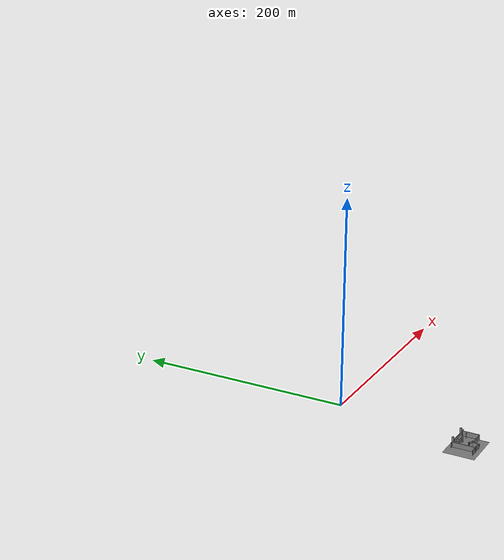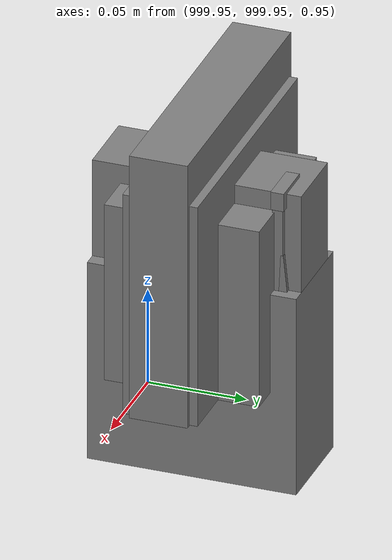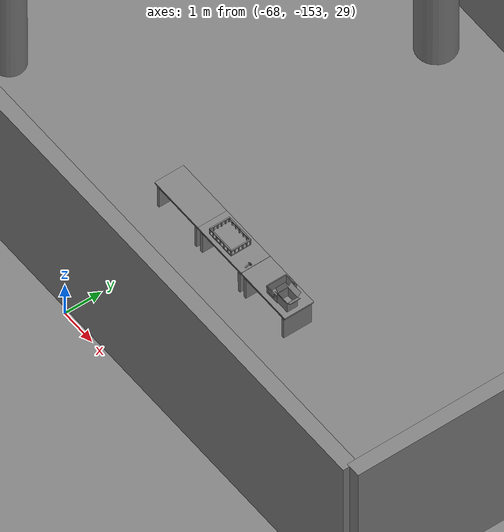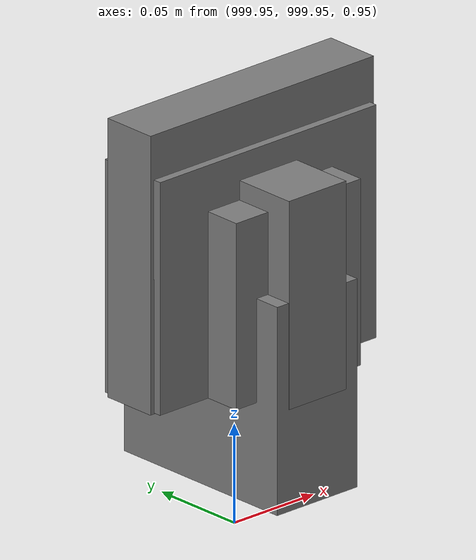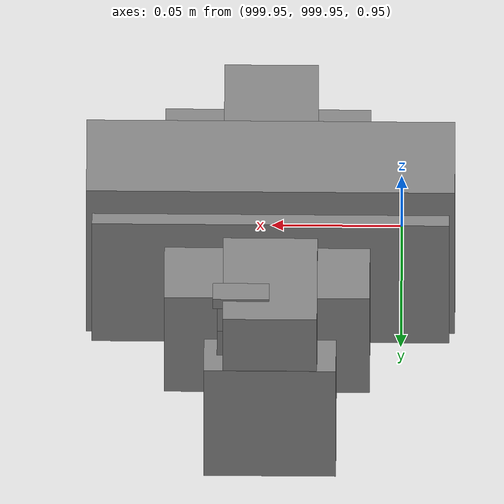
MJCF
<mujoco>
    <option gravity="0.000000000 0.000000000 -9.810000420" timestep="0.0049999999" integrator="implicitfast" density="1.225" viscosity="1.8000001e-05" noslip_iterations="10" iterations="100" sdf_iterations="50">
        <flag multiccd="disable"/>
    </option>
    <size memory="1000M"/>
    <compiler coordinate="local"/>
    <worldbody>
        <light cutoff="30" pos="0 1 1" dir="0 -1 -2"/>
        <light cutoff="30" pos="0 -1 1" dir="0 1 -2"/>
        <body pos="1000.000000000 1000.000000000 1.000000000" euler="0.000000000 0.000000000 180.000000000" name="openloong_gripper_2f85_fix_base_usda_wifi_box">
            <geom contype="1" conaffinity="1" density="1000" type="box" material="" rgba="0.500000000 0.500000000 0.500000000 1.000000000" solimp="0.899999976 0.949999988 0.001000000" friction="1.000000000 0.005000000 0.000100000" solref="0.020000000 1.000000000" margin="0" condim="3" group="0" pos="0.000000000 0.000000000 0.058978677" quat="0.000000000 0.000000047 0.000000000 1.000000000" size="0.068499997 0.018999999 0.059000000" name="openloong_gripper_2f85_fix_base_usda_geom_70701682_A9F8_4EF2_841B_3D702D049598"/>
            <freejoint name="openloong_gripper_2f85_fix_base_usda_wifi_box_joint"/>
            <site size="0.005000000 0.005000000 0.005000000" rgba="0.500000000 0.500000000 0.500000000 1.000000000" pos="0.000000000 0.000000000 0.000000000" quat="0.999961913 0.008726500 0.000000000 0.000000000" group="0" type="sphere" name="openloong_gripper_2f85_fix_base_usda_wifi_boxsite"/>
        </body>
        <body pos="1000.000000000 1000.000000000 1.000000000" euler="0.000011953 0.000005123 -179.999984741" name="openloong_gripper_2f85_fix_base_usda_intel_box">
            <geom contype="1" conaffinity="1" density="1000" type="box" material="" rgba="0.500000000 0.500000000 0.500000000 1.000000000" solimp="0.899999976 0.949999988 0.001000000" friction="1.000000000 0.005000000 0.000100000" solref="0.020000000 1.000000000" margin="0" condim="3" group="0" pos="0.000000000 -0.000067139 0.000082284" quat="0.707106709 0.000000225 0.000000253 0.707106650" size="0.052800003 0.025300000 0.052800003" name="openloong_gripper_2f85_fix_base_usda_geom_7AC0D242_97D9_4581_8687_6C63465BCCAA"/>
            <freejoint name="openloong_gripper_2f85_fix_base_usda_intel_box_joint"/>
            <site size="0.005000000 0.005000000 0.005000000" rgba="0.500000000 0.500000000 0.500000000 1.000000000" pos="0.000000000 0.000000000 0.000000000" quat="0.999961913 0.008726500 0.000000000 0.000000000" group="0" type="sphere" name="openloong_gripper_2f85_fix_base_usda_intel_boxsite"/>
        </body>
        <body pos="-66.352325439 -149.268768311 31.171619415" euler="-151.483581543 -16.663696289 10.195839882" mocap="true" name="spotlight6_SpotLight"/>
        <body pos="1000.000000000 1000.000000000 1.000000000" euler="0.000000000 0.000000000 180.000000000" name="openloong_gripper_2f85_fix_base_usda_cpu_fan">
            <geom contype="1" conaffinity="1" density="1000" type="box" material="" rgba="0.500000000 0.500000000 0.500000000 1.000000000" solimp="0.899999976 0.949999988 0.001000000" friction="1.000000000 0.005000000 0.000100000" solref="0.020000000 1.000000000" margin="0" condim="3" group="0" pos="0.000000000 0.000000000 0.070034981" quat="0.000000000 0.000000000 0.000000000 1.000000000" size="0.070700005 0.014699999 0.070700005" name="openloong_gripper_2f85_fix_base_usda_geom_2878D638_486E_40DC_9EB0_868AA6FDEF35"/>
            <freejoint name="openloong_gripper_2f85_fix_base_usda_cpu_fan_joint"/>
            <site size="0.005000000 0.005000000 0.005000000" rgba="0.500000000 0.500000000 0.500000000 1.000000000" pos="0.000000000 0.000000000 0.000000000" quat="0.999961913 0.008726535 0.000000000 0.000000000" group="0" type="sphere" name="openloong_gripper_2f85_fix_base_usda_cpu_fancsite"/>
        </body>
        <body pos="1000.000000000 999.999938965 1.000000000" euler="0.000000000 0.000000000 180.000000000" name="openloong_gripper_2f85_fix_base_usda_intelcore_i5">
            <geom contype="1" conaffinity="1" density="1000" type="box" material="" rgba="0.500000000 0.500000000 0.500000000 1.000000000" solimp="0.899999976 0.949999988 0.001000000" friction="1.000000000 0.005000000 0.000100000" solref="0.020000000 1.000000000" margin="0" condim="3" group="0" pos="0.000000000 0.000000000 0.051722717" quat="0.707106709 0.000000000 0.000000000 -0.707106769" size="0.052800000 0.018080002 0.052800000" name="openloong_gripper_2f85_fix_base_usda_geom_CFEB3B7B_C345_41F3_AD09_C97801C23EAA"/>
            <freejoint name="openloong_gripper_2f85_fix_base_usda_intelcore_i5_joint"/>
            <site size="0.005000000 0.005000000 0.005000000" rgba="0.500000000 0.500000000 0.500000000 1.000000000" pos="0.000000000 0.000000000 0.000000000" quat="0.999961913 0.008726534 0.000000000 0.000000000" group="0" type="sphere" name="openloong_gripper_2f85_fix_base_usda_intelcore_i5site"/>
        </body>
        <body pos="-66.218811035 -149.095886230 31.168849945" euler="-142.748397827 89.946166992 -24.750513077" mocap="true" name="spotlight2_SpotLight"/>
        <body pos="-66.316802979 -149.474960327 31.170793533" euler="-54.815830231 2.397670746 -136.065231323" mocap="true" name="spotlight3_SpotLight"/>
        <body pos="1000.000000000 1000.000000000 1.000000000" euler="0.000000000 0.000000000 180.000000000" name="openloong_gripper_2f85_fix_base_usda_battery_01">
            <geom contype="1" conaffinity="1" density="1000" type="box" material="" rgba="0.500000000 0.500000000 0.500000000 1.000000000" solimp="0.899999976 0.949999988 0.001000000" friction="1.000000000 0.005000000 0.000100000" solref="0.020000000 1.000000000" margin="0" condim="3" group="0" pos="-0.011123657 -0.041940309 0.101691343" quat="1.000000000 0.000000000 0.000000000 0.000000000" size="0.010800000 0.003375000 0.004725000" name="openloong_gripper_2f85_fix_base_usda_geom_BDF3D353_930F_45D9_9710_6359D0AEBFEC"/>
            <geom contype="1" conaffinity="1" density="1000" type="box" material="" rgba="0.500000000 0.500000000 0.500000000 1.000000000" solimp="0.899999976 0.949999988 0.001000000" friction="1.000000000 0.005000000 0.000100000" solref="0.020000000 1.000000000" margin="0" condim="3" group="0" pos="-0.010876465 -0.044247437 0.047066893" quat="0.998702705 -0.050920475 0.000000000 0.000000000" size="0.009450001 0.002700000 0.024975000" name="openloong_gripper_2f85_fix_base_usda_geom_8111DE2E_41A9_4FD6_824E_125A5DE03293"/>
            <geom contype="1" conaffinity="1" density="1000" type="box" material="" rgba="0.500000000 0.500000000 0.500000000 1.000000000" solimp="0.899999976 0.949999988 0.001000000" friction="1.000000000 0.005000000 0.000100000" solref="0.020000000 1.000000000" margin="0" condim="3" group="0" pos="-0.001235962 -0.000659180 0.047381196" quat="1.000000000 0.000000000 0.000000000 0.000000000" size="0.039420001 0.039150000 0.047250003" name="openloong_gripper_2f85_fix_base_usda_geom_1F711335_F21F_4C44_B330_3F976283573E"/>
            <geom contype="1" conaffinity="1" density="1000" type="box" material="" rgba="0.500000000 0.500000000 0.500000000 1.000000000" solimp="0.899999976 0.949999988 0.001000000" friction="1.000000000 0.005000000 0.000100000" solref="0.020000000 1.000000000" margin="0" condim="3" group="0" pos="-0.010876465 -0.039138794 0.009851727" quat="1.000000000 0.000000000 0.000000000 0.000000000" size="0.009450001 0.010800000 0.013500000" name="openloong_gripper_2f85_fix_base_usda_geom_1461B342_887E_4ADB_8823_BE2AA9E5FD4C"/>
            <geom contype="1" conaffinity="1" density="1000" type="box" material="" rgba="0.500000000 0.500000000 0.500000000 1.000000000" solimp="0.899999976 0.949999988 0.001000000" friction="1.000000000 0.005000000 0.000100000" solref="0.020000000 1.000000000" margin="0" condim="3" group="0" pos="-0.010876465 -0.041528322 0.071508206" quat="1.000000000 0.000000000 0.000000000 0.000000000" size="0.009450001 0.002700000 0.027000001" name="openloong_gripper_2f85_fix_base_usda_geom_9DCA238B_3A31_43BE_9CDB_7EF965D8D360"/>
            <freejoint name="openloong_gripper_2f85_fix_base_usda_battery_01_joint"/>
            <site size="0.005000000 0.005000000 0.005000000" rgba="0.500000000 0.500000000 0.500000000 1.000000000" pos="0.000000000 0.000000000 0.000000000" quat="0.999961913 0.008726500 0.000000000 0.000000000" group="0" type="sphere" name="openloong_gripper_2f85_fix_base_usda_battery_01site"/>
        </body>
        <body pos="-64.866622925 -149.383972168 30.183746338" euler="89.999984741 89.999946594 0.000000000" name="openloong_gripper_2f85_fix_base_usda_bluebox_01">
            <geom contype="1" conaffinity="1" density="1000" type="box" material="" rgba="0.500000000 0.500000000 0.500000000 1.000000000" solimp="0.899999976 0.949999988 0.001000000" friction="1.000000000 0.005000000 0.000100000" solref="0.020000000 1.000000000" margin="0" condim="3" group="0" pos="0.276580811 0.187225342 0.000068665" quat="0.707106948 0.000077471 0.707106352 0.000077486" size="0.100000001 0.057999998 0.010000000" name="openloong_gripper_2f85_fix_base_usda_geom_7DF90487_8F38_493F_BFE8_8E4385C2911C"/>
            <geom contype="1" conaffinity="1" density="1000" type="box" material="" rgba="0.500000000 0.500000000 0.500000000 1.000000000" solimp="0.899999976 0.949999988 0.001000000" friction="1.000000000 0.005000000 0.000100000" solref="0.020000000 1.000000000" margin="0" condim="3" group="0" pos="0.000000000 0.002883911 0.000000000" quat="0.999999881 0.000000000 0.000000000 0.000000000" size="0.254000008 0.003000000 0.172000006" name="openloong_gripper_2f85_fix_base_usda_geom_017EF62C_B96E_44EE_8CEC_49936CCEA2F7"/>
            <geom contype="1" conaffinity="1" density="1000" type="box" material="" rgba="0.500000000 0.500000000 0.500000000 1.000000000" solimp="0.899999976 0.949999988 0.001000000" friction="1.000000000 0.005000000 0.000100000" solref="0.020000000 1.000000000" margin="0" condim="3" group="0" pos="0.000000000 0.124874115 0.173484802" quat="0.999796331 0.020176515 -0.000000015 0.000000030" size="0.259999990 0.119999997 0.007000000" name="openloong_gripper_2f85_fix_base_usda_geom_8D9B1F66_B412_4EC3_8194_3036C5D43C08"/>
            <geom contype="1" conaffinity="1" density="1000" type="box" material="" rgba="0.500000000 0.500000000 0.500000000 1.000000000" solimp="0.899999976 0.949999988 0.001000000" friction="1.000000000 0.005000000 0.000100000" solref="0.020000000 1.000000000" margin="0" condim="3" group="0" pos="0.000000000 0.124874115 -0.173469543" quat="0.999796331 -0.020176545 -0.000000015 0.000000000" size="0.259999990 0.119999997 0.007000000" name="openloong_gripper_2f85_fix_base_usda_geom_C54A4CE1_37B0_47F4_8E5E_D8EE77D3CDA1"/>
            <geom contype="1" conaffinity="1" density="1000" type="box" material="" rgba="0.500000000 0.500000000 0.500000000 1.000000000" solimp="0.899999976 0.949999988 0.001000000" friction="1.000000000 0.005000000 0.000100000" solref="0.020000000 1.000000000" margin="0" condim="3" group="0" pos="0.000000000 0.214008331 0.188980103" quat="0.999912977 0.013176724 0.000000015 0.000000000" size="0.259999990 0.029999999 0.012500000" name="openloong_gripper_2f85_fix_base_usda_geom_E0B58002_42F4_403B_AF36_DD90423543AB"/>
            <geom contype="1" conaffinity="1" density="1000" type="box" material="" rgba="0.500000000 0.500000000 0.500000000 1.000000000" solimp="0.899999976 0.949999988 0.001000000" friction="1.000000000 0.005000000 0.000100000" solref="0.020000000 1.000000000" margin="0" condim="3" group="0" pos="-0.258361816 0.125289917 0.001876831" quat="0.702796936 -0.020792112 0.710783124 0.020769298" size="0.189999998 0.119999997 0.009000000" name="openloong_gripper_2f85_fix_base_usda_geom_AC63C551_236D_4FD9_8FAE_7B3733C4D02B"/>
            <geom contype="1" conaffinity="1" density="1000" type="box" material="" rgba="0.500000000 0.500000000 0.500000000 1.000000000" solimp="0.899999976 0.949999988 0.001000000" friction="1.000000000 0.005000000 0.000100000" solref="0.020000000 1.000000000" margin="0" condim="3" group="0" pos="0.000000000 0.214008331 -0.188980103" quat="0.999912977 -0.013176769 0.000000030 0.000000015" size="0.259999990 0.029999999 0.012500000" name="openloong_gripper_2f85_fix_base_usda_geom_76D4D347_9A3F_46D0_8159_89D59F2431E2"/>
            <geom contype="1" conaffinity="1" density="1000" type="box" material="" rgba="0.500000000 0.500000000 0.500000000 1.000000000" solimp="0.899999976 0.949999988 0.001000000" friction="1.000000000 0.005000000 0.000100000" solref="0.020000000 1.000000000" margin="0" condim="3" group="0" pos="-0.276611328 0.187225342 0.000068665" quat="0.707106650 0.000077441 0.707106709 0.000077456" size="0.100000001 0.057999998 0.010000000" name="openloong_gripper_2f85_fix_base_usda_geom_D7B624DE_2D19_43F2_9399_6C8F8195EDF9"/>
            <geom contype="1" conaffinity="1" density="1000" type="box" material="" rgba="0.500000000 0.500000000 0.500000000 1.000000000" solimp="0.899999976 0.949999988 0.001000000" friction="1.000000000 0.005000000 0.000100000" solref="0.020000000 1.000000000" margin="0" condim="3" group="0" pos="0.258331299 0.125289917 0.001876831" quat="0.702851415 0.018856421 0.710823774 -0.019329369" size="0.189999998 0.119999997 0.009000000" name="openloong_gripper_2f85_fix_base_usda_geom_ACD1204C_0FB6_4034_BDB4_0000EFFC5AAE"/>
            <freejoint name="openloong_gripper_2f85_fix_base_usda_bluebox_01_joint"/>
            <site size="0.005000000 0.005000000 0.005000000" rgba="0.500000000 0.500000000 0.500000000 1.000000000" pos="0.000000000 0.000000000 0.000000000" quat="0.999961913 0.008726534 0.000000000 0.000000000" group="0" type="sphere" name="openloong_gripper_2f85_fix_base_usda_bluebox_01site"/>
        </body>
        <body pos="-64.496299744 -149.491867065 30.235729218" euler="0.000000000 0.000000000 89.999946594" name="openloong_gripper_2f85_fix_base_usda_cardboardbox_01">
            <geom contype="1" conaffinity="1" density="1000" type="box" material="" rgba="0.500000000 0.500000000 0.500000000 1.000000000" solimp="0.899999976 0.949999988 0.001000000" friction="1.000000000 0.005000000 0.000100000" solref="0.020000000 1.000000000" margin="0" condim="3" group="0" pos="-0.003166199 -0.004086494 0.005052090" quat="1.000000000 0.000000000 0.000000000 0.000000000" size="0.142499998 0.177500010 0.005000000" name="openloong_gripper_2f85_fix_base_usda_geom_4F755AEC_1367_40D3_B3D2_B4AB69B1CFF9"/>
            <geom contype="1" conaffinity="1" density="1000" type="box" material="" rgba="0.500000000 0.500000000 0.500000000 1.000000000" solimp="0.899999976 0.949999988 0.001000000" friction="1.000000000 0.005000000 0.000100000" solref="0.020000000 1.000000000" margin="0" condim="3" group="0" pos="-0.003166199 0.170316696 0.150570869" quat="1.000000000 0.000000000 0.000000000 0.000000000" size="0.142499998 0.005000000 0.149999991" name="openloong_gripper_2f85_fix_base_usda_geom_2095C588_2171_4A8A_A672_567B769F4479"/>
            <geom contype="1" conaffinity="1" density="1000" type="box" material="" rgba="0.500000000 0.500000000 0.500000000 1.000000000" solimp="0.899999976 0.949999988 0.001000000" friction="1.000000000 0.005000000 0.000100000" solref="0.020000000 1.000000000" margin="0" condim="3" group="0" pos="-0.147399902 -0.005307198 0.150570869" quat="1.000000000 0.000000000 0.000000000 0.000000000" size="0.005000000 0.177500010 0.149999991" name="openloong_gripper_2f85_fix_base_usda_geom_37C65B89_DDC8_4EDF_BBB1_E093B2961CB7"/>
            <geom contype="1" conaffinity="1" density="1000" type="box" material="" rgba="0.500000000 0.500000000 0.500000000 1.000000000" solimp="0.899999976 0.949999988 0.001000000" friction="1.000000000 0.005000000 0.000100000" solref="0.020000000 1.000000000" margin="0" condim="3" group="0" pos="0.140275955 -0.005307198 0.150570869" quat="1.000000000 0.000000000 0.000000000 0.000000000" size="0.005000000 0.177500010 0.149999991" name="openloong_gripper_2f85_fix_base_usda_geom_834FDE8B_C865_4261_BC20_F8D6F651F78F"/>
            <geom contype="1" conaffinity="1" density="1000" type="box" material="" rgba="0.500000000 0.500000000 0.500000000 1.000000000" solimp="0.899999976 0.949999988 0.001000000" friction="1.000000000 0.005000000 0.000100000" solref="0.020000000 1.000000000" margin="0" condim="3" group="0" pos="-0.003166199 -0.181550980 0.150570869" quat="1.000000000 0.000000000 0.000000000 0.000000000" size="0.142499998 0.005000000 0.149999991" name="openloong_gripper_2f85_fix_base_usda_geom_409464EF_D0F7_4C76_80B1_C002E378F6A2"/>
            <freejoint name="openloong_gripper_2f85_fix_base_usda_cardboardbox_01_joint"/>
            <site size="0.005000000 0.005000000 0.005000000" rgba="0.500000000 0.500000000 0.500000000 1.000000000" pos="0.000000000 0.000000000 0.000000000" quat="0.999961913 0.008726535 0.000000000 0.000000000" group="0" type="sphere" name="openloong_gripper_2f85_fix_base_usda_site_21B41FB1_D214_4D06_BB0C_1A87B99EE4ED"/>
            <body pos="0.139160156 -0.004048347 0.301930904" euler="-179.999954224 49.383502960 179.999954224" name="openloong_gripper_2f85_fix_base_usda_A1_006">
                <geom contype="1" conaffinity="1" density="1000" type="box" material="" rgba="0.500000000 0.500000000 0.500000000 1.000000000" solimp="0.899999976 0.949999988 0.001000000" friction="1.000000000 0.005000000 0.000100000" solref="0.020000000 1.000000000" margin="0" condim="3" group="0" pos="-0.071587563 0.000009537 0.001745224" quat="0.999999881 0.000000000 0.000000000 0.000000000" size="0.071249999 0.179999992 0.002500000" name="openloong_gripper_2f85_fix_base_usda_geom_BA9FA250_C988_4AF3_9476_5BE4B5B381B2"/>
                <joint armature="0" stiffness="0.07" damping="0.0099999998" axis="0.000000 1.000000 0.000000" type="hinge" name="openloong_gripper_2f85_fix_base_usda_A1_006"/>
            </body>
            <body pos="-0.145902634 -0.004086494 0.301938057" euler="-180.000000000 -60.000011444 -180.000000000" name="openloong_gripper_2f85_fix_base_usda_A2_006">
                <geom contype="1" conaffinity="1" density="1000" type="box" material="" rgba="0.500000000 0.500000000 0.500000000 1.000000000" solimp="0.899999976 0.949999988 0.001000000" friction="1.000000000 0.005000000 0.000100000" solref="0.020000000 1.000000000" margin="0" condim="3" group="0" pos="0.071268082 0.000009537 0.002717972" quat="0.000002921 0.000000000 -0.000000030 0.999999881" size="0.071249999 0.179999992 0.002500000" name="openloong_gripper_2f85_fix_base_usda_geom_71A6B2E1_265D_4744_8785_4178B3E5E44C"/>
                <joint armature="0" stiffness="0.07" damping="0.0099999998" axis="0.000000 1.000000 0.000000" type="hinge" name="openloong_gripper_2f85_fix_base_usda_A2_006"/>
            </body>
            <body pos="-0.003385544 0.175991058 0.301930904" euler="-125.858116150 -0.000004561 0.000002331" name="openloong_gripper_2f85_fix_base_usda_B2_006">
                <geom contype="1" conaffinity="1" density="1000" type="box" material="" rgba="0.500000000 0.500000000 0.500000000 1.000000000" solimp="0.899999976 0.949999988 0.001000000" friction="1.000000000 0.005000000 0.000100000" solref="0.020000000 1.000000000" margin="0" condim="3" group="0" pos="0.000009537 -0.070939064 -0.002470016" quat="0.999614120 0.027776197 -0.000000015 0.000000030" size="0.137500003 0.064999998 0.005000000" name="openloong_gripper_2f85_fix_base_usda_geom_F3A7D417_F721_4050_A74A_A974BA1DFE21"/>
                <joint armature="0" stiffness="0.07" damping="0.0099999998" axis="1.000000 0.000000 0.000000" type="hinge" name="openloong_gripper_2f85_fix_base_usda_B2_006"/>
            </body>
            <body pos="-0.003385544 -0.184140205 0.301938057" euler="147.805557251 0.000000000 0.000000000" name="openloong_gripper_2f85_fix_base_usda_B1_006">
                <geom contype="1" conaffinity="1" density="1000" type="box" material="" rgba="0.500000000 0.500000000 0.500000000 1.000000000" solimp="0.899999976 0.949999988 0.001000000" friction="1.000000000 0.005000000 0.000100000" solref="0.020000000 1.000000000" margin="0" condim="3" group="0" pos="-0.000028610 0.070202351 -0.002703667" quat="0.999614179 -0.027776167 0.000000000 0.000000000" size="0.137500003 0.064999998 0.005000000" name="openloong_gripper_2f85_fix_base_usda_geom_A21C96BB_DECD_4044_B30F_DF63660DCEF8"/>
                <joint armature="0" stiffness="0.07" damping="0.0099999998" axis="1.000000 0.000000 0.000000" type="hinge" name="openloong_gripper_2f85_fix_base_usda_B1_006"/>
            </body>
        </body>
        <body pos="-65.882858276 -149.481979370 30.229999542" euler="-64.487716675 0.000000000 0.000000000" name="openloong_gripper_2f85_fix_base_usda_Barcode">
            <geom contype="1" conaffinity="1" density="1000" type="box" material="" rgba="0.500000000 0.500000000 0.500000000 1.000000000" solimp="0.899999976 0.949999988 0.001000000" friction="1.000000000 0.005000000 0.000100000" solref="0.020000000 1.000000000" margin="0" condim="3" group="0" pos="0.000000000 0.013038635 0.001419067" quat="0.000000000 0.000000000 0.000000000 1.000000119" size="0.034000002 0.010000000 0.017999999" name="openloong_gripper_2f85_fix_base_usda_geom_8F898284_4D8C_4DAF_9410_E272E9107D0C"/>
            <geom contype="1" conaffinity="1" density="1000" type="box" material="" rgba="0.500000000 0.500000000 0.500000000 1.000000000" solimp="0.899999976 0.949999988 0.001000000" friction="1.000000000 0.005000000 0.000100000" solref="0.020000000 1.000000000" margin="0" condim="3" group="0" pos="0.000000000 -0.035301208 -0.007095337" quat="0.000000000 0.000000000 -0.043619365 0.999048233" size="0.028999999 0.010000000 0.020000000" name="openloong_gripper_2f85_fix_base_usda_geom_49ABA77B_3A99_4234_BFEE_E717522F7812"/>
            <geom contype="1" conaffinity="1" density="1000" type="box" material="" rgba="0.500000000 0.500000000 0.500000000 1.000000000" solimp="0.899999976 0.949999988 0.001000000" friction="1.000000000 0.005000000 0.000100000" solref="0.020000000 1.000000000" margin="0" condim="3" group="0" pos="0.000000000 -0.043411255 -0.011749268" quat="0.922262907 0.386563420 0.000000000 0.000000000" size="0.026000001 0.010000000 0.020000000" name="openloong_gripper_2f85_fix_base_usda_geom_AE45858D_242A_4480_89D4_7E7CCCC5A1C3"/>
            <geom contype="1" conaffinity="1" density="1000" type="box" material="" rgba="0.500000000 0.500000000 0.500000000 1.000000000" solimp="0.899999976 0.949999988 0.001000000" friction="1.000000000 0.005000000 0.000100000" solref="0.020000000 1.000000000" margin="0" condim="3" group="0" pos="0.000000000 -0.016967773 -0.031860352" quat="0.000000000 0.000000000 0.000000000 1.000000119" size="0.008000000 0.010000000 0.013000000" name="openloong_gripper_2f85_fix_base_usda_geom_21CDF711_210A_422B_A043_519FAE6EBFDE"/>
            <geom contype="1" conaffinity="1" density="1000" type="box" material="" rgba="0.500000000 0.500000000 0.500000000 1.000000000" solimp="0.899999976 0.949999988 0.001000000" friction="1.000000000 0.005000000 0.000100000" solref="0.020000000 1.000000000" margin="0" condim="3" group="0" pos="0.000000000 -0.001869202 0.000312805" quat="0.953716993 0.300705761 0.000000000 0.000000000" size="0.032000002 0.010000000 0.018999999" name="openloong_gripper_2f85_fix_base_usda_geom_64098372_4650_458D_9280_166F44042C47"/>
            <geom contype="1" conaffinity="1" density="1000" type="box" material="" rgba="0.500000000 0.500000000 0.500000000 1.000000000" solimp="0.899999976 0.949999988 0.001000000" friction="1.000000000 0.005000000 0.000100000" solref="0.020000000 1.000000000" margin="0" condim="3" group="0" pos="0.000000000 -0.019531250 -0.003173828" quat="0.953716993 0.300705761 0.000000000 0.000000000" size="0.030999999 0.010000000 0.020000000" name="openloong_gripper_2f85_fix_base_usda_geom_2A431905_4EA0_47A7_ABB7_DBC06628BB1A"/>
            <geom contype="1" conaffinity="1" density="1000" type="box" material="" rgba="0.500000000 0.500000000 0.500000000 1.000000000" solimp="0.899999976 0.949999988 0.001000000" friction="1.000000000 0.005000000 0.000100000" solref="0.020000000 1.000000000" margin="0" condim="3" group="0" pos="0.000000000 -0.035301208 -0.007095337" quat="0.953716993 0.300705761 0.000000000 0.000000000" size="0.028999999 0.010000000 0.020000000" name="openloong_gripper_2f85_fix_base_usda_geom_DC0F7E67_5A5C_4F8F_9474_DE5E7EA8A468"/>
            <geom contype="1" conaffinity="1" density="1000" type="box" material="" rgba="0.500000000 0.500000000 0.500000000 1.000000000" solimp="0.899999976 0.949999988 0.001000000" friction="1.000000000 0.005000000 0.000100000" solref="0.020000000 1.000000000" margin="0" condim="3" group="0" pos="0.000000000 -0.042617798 -0.071121216" quat="0.000000000 0.000000000 0.000000000 1.000000119" size="0.013000000 0.021000000 0.059999999" name="openloong_gripper_2f85_fix_base_usda_geom_07D8928F_391F_48A4_AC0E_04A392C47E59"/>
            <freejoint name="openloong_gripper_2f85_fix_base_usda_Barcode_joint"/>
            <site size="0.005000000 0.005000000 0.005000000" rgba="0.500000000 0.500000000 0.500000000 1.000000000" pos="0.000000000 0.000000000 0.000000000" quat="1.000000000 0.000000000 0.000000000 0.000000000" group="0" type="sphere" name="openloong_gripper_2f85_fix_base_usda_Barcode_site"/>
        </body>
        <body pos="-66.745018005 -149.392349243 30.184000015" euler="0.000000000 0.000000000 89.999946594" name="[22333494571744]_Basket_01">
            <geom contype="1" conaffinity="1" density="1000" type="box" material="" rgba="0.500000000 0.500000000 0.500000000 1.000000000" solimp="0.899999976 0.949999988 0.001000000" friction="1.000000000 0.005000000 0.000100000" solref="0.020000000 1.000000000" margin="0" condim="3" group="0" pos="-0.052425385 0.389207840 0.089787483" quat="0.707107008 0.000000000 0.000000000 0.707106411" size="0.014249999 0.014249999 0.059999999" name="[22333494571744]_geom_0776F674_4E96_4933_BA29_9E226AD33B5C"/>
            <geom contype="1" conaffinity="1" density="1000" type="box" material="" rgba="0.500000000 0.500000000 0.500000000 1.000000000" solimp="0.899999976 0.949999988 0.001000000" friction="1.000000000 0.005000000 0.000100000" solref="0.020000000 1.000000000" margin="0" condim="3" group="0" pos="0.264015198 -0.133043289 0.089787483" quat="0.707107008 0.000000000 0.000000000 0.707106411" size="0.014249999 0.014249999 0.059999999" name="[22333494571744]_geom_BDB0D45D_A8D9_4CDD_BDA7_A768AE502DB3"/>
            <geom contype="1" conaffinity="1" density="1000" type="box" material="" rgba="0.500000000 0.500000000 0.500000000 1.000000000" solimp="0.899999976 0.949999988 0.001000000" friction="1.000000000 0.005000000 0.000100000" solref="0.020000000 1.000000000" margin="0" condim="3" group="0" pos="-0.264015198 -0.265548706 0.089793205" quat="0.707107008 0.000000000 0.000000000 0.707106411" size="0.014249999 0.014249999 0.059999999" name="[22333494571744]_geom_394061C5_3389_440A_844C_7B30C03BCDDC"/>
            <geom contype="1" conaffinity="1" density="1000" type="box" material="" rgba="0.500000000 0.500000000 0.500000000 1.000000000" solimp="0.899999976 0.949999988 0.001000000" friction="1.000000000 0.005000000 0.000100000" solref="0.020000000 1.000000000" margin="0" condim="3" group="0" pos="-0.160263062 -0.389322281 0.089793205" quat="0.707107008 0.000000000 0.000000000 0.707106411" size="0.014249999 0.014249999 0.059999999" name="[22333494571744]_geom_05CBD754_2AAC_4BE2_8A24_52AE9A565D5A"/>
            <geom contype="1" conaffinity="1" density="1000" type="box" material="" rgba="0.500000000 0.500000000 0.500000000 1.000000000" solimp="0.899999976 0.949999988 0.001000000" friction="1.000000000 0.005000000 0.000100000" solref="0.020000000 1.000000000" margin="0" condim="3" group="0" pos="0.162265778 -0.389322281 0.089787483" quat="0.707107008 0.000000000 0.000000000 0.707106411" size="0.014249999 0.014249999 0.059999999" name="[22333494571744]_geom_576B9B3B_D789_4872_8FA3_160195316E2C"/>
            <geom contype="1" conaffinity="1" density="1000" type="box" material="" rgba="0.500000000 0.500000000 0.500000000 1.000000000" solimp="0.899999976 0.949999988 0.001000000" friction="1.000000000 0.005000000 0.000100000" solref="0.020000000 1.000000000" margin="0" condim="3" group="0" pos="0.264015198 0.389207840 0.089787483" quat="0.707107008 0.000000000 0.000000000 0.707106411" size="0.014249999 0.014249999 0.059999999" name="[22333494571744]_geom_185358D0_6752_40A4_A594_D8D9114C0221"/>
            <geom contype="1" conaffinity="1" density="1000" type="box" material="" rgba="0.500000000 0.500000000 0.500000000 1.000000000" solimp="0.899999976 0.949999988 0.001000000" friction="1.000000000 0.005000000 0.000100000" solref="0.020000000 1.000000000" margin="0" condim="3" group="0" pos="-0.264015198 -0.133043289 0.089793205" quat="0.707107008 0.000000000 0.000000000 0.707106411" size="0.014249999 0.014249999 0.059999999" name="[22333494571744]_geom_2AC41ABF_53FE_4466_80F5_8A19B7664225"/>
            <geom contype="1" conaffinity="1" density="1000" type="box" material="" rgba="0.500000000 0.500000000 0.500000000 1.000000000" solimp="0.899999976 0.949999988 0.001000000" friction="1.000000000 0.005000000 0.000100000" solref="0.020000000 1.000000000" margin="0" condim="3" group="0" pos="-0.264026642 0.269256592 0.089793205" quat="0.707107008 0.000000000 0.000000000 0.707106411" size="0.014249999 0.014249999 0.059999999" name="[22333494571744]_geom_383FC1C5_54FE_4B50_BEED_F569BB1C6310"/>
            <geom contype="1" conaffinity="1" density="1000" type="box" material="" rgba="0.500000000 0.500000000 0.500000000 1.000000000" solimp="0.899999976 0.949999988 0.001000000" friction="1.000000000 0.005000000 0.000100000" solref="0.020000000 1.000000000" margin="0" condim="3" group="0" pos="0.054462433 0.389207840 0.089787483" quat="0.707107008 0.000000000 0.000000000 0.707106411" size="0.014249999 0.014249999 0.059999999" name="[22333494571744]_geom_C212297E_3D82_43D0_A1DA_4E92B592F99A"/>
            <geom contype="1" conaffinity="1" density="1000" type="box" material="" rgba="0.500000000 0.500000000 0.500000000 1.000000000" solimp="0.899999976 0.949999988 0.001000000" friction="1.000000000 0.005000000 0.000100000" solref="0.020000000 1.000000000" margin="0" condim="3" group="0" pos="0.054462433 -0.389322281 0.089787483" quat="0.707107008 0.000000000 0.000000000 0.707106411" size="0.014249999 0.014249999 0.059999999" name="[22333494571744]_geom_282F06C6_89C9_4F4C_96B9_627DD32AA001"/>
            <geom contype="1" conaffinity="1" density="1000" type="box" material="" rgba="0.500000000 0.500000000 0.500000000 1.000000000" solimp="0.899999976 0.949999988 0.001000000" friction="1.000000000 0.005000000 0.000100000" solref="0.020000000 1.000000000" margin="0" condim="3" group="0" pos="0.264015198 0.269256592 0.089793205" quat="0.707107008 0.000000000 0.000000000 0.707106411" size="0.014249999 0.014249999 0.059999999" name="[22333494571744]_geom_E1B32E4E_E1F4_42FD_9E7F_BF7B80110410"/>
            <geom contype="1" conaffinity="1" density="1000" type="box" material="" rgba="0.500000000 0.500000000 0.500000000 1.000000000" solimp="0.899999976 0.949999988 0.001000000" friction="1.000000000 0.005000000 0.000100000" solref="0.020000000 1.000000000" margin="0" condim="3" group="0" pos="0.264015198 -0.389322281 0.089787483" quat="0.707107008 0.000000000 0.000000000 0.707106411" size="0.014249999 0.014249999 0.059999999" name="[22333494571744]_geom_8F9D18D3_647E_4057_A31C_C3EE2AE9BA47"/>
            <geom contype="1" conaffinity="1" density="1000" type="box" material="" rgba="0.500000000 0.500000000 0.500000000 1.000000000" solimp="0.899999976 0.949999988 0.001000000" friction="1.000000000 0.005000000 0.000100000" solref="0.020000000 1.000000000" margin="0" condim="3" group="0" pos="0.000000000 0.000000000 0.015998840" quat="0.707107008 0.000000000 0.000000000 0.707106411" size="0.403499991 0.279000014 0.015750000" name="[22333494571744]_geom_8C7A6500_7118_49D3_A101_71972E489D6E"/>
            <geom contype="1" conaffinity="1" density="1000" type="box" material="" rgba="0.500000000 0.500000000 0.500000000 1.000000000" solimp="0.899999976 0.949999988 0.001000000" friction="1.000000000 0.005000000 0.000100000" solref="0.020000000 1.000000000" margin="0" condim="3" group="0" pos="0.000000000 -0.389476776 0.163619041" quat="0.707107008 0.000000000 0.000000000 0.707106411" size="0.015000000 0.277500004 0.015750000" name="[22333494571744]_geom_B77B95F3_7BF9_470B_B291_2D6AADACE341"/>
            <geom contype="1" conaffinity="1" density="1000" type="box" material="" rgba="0.500000000 0.500000000 0.500000000 1.000000000" solimp="0.899999976 0.949999988 0.001000000" friction="1.000000000 0.005000000 0.000100000" solref="0.020000000 1.000000000" margin="0" condim="3" group="0" pos="0.162265778 0.389207840 0.089787483" quat="0.707107008 0.000000000 0.000000000 0.707106411" size="0.014249999 0.014249999 0.059999999" name="[22333494571744]_geom_09A7BA21_F2AC_4924_AB8B_4B59B8D46A9B"/>
            <geom contype="1" conaffinity="1" density="1000" type="box" material="" rgba="0.500000000 0.500000000 0.500000000 1.000000000" solimp="0.899999976 0.949999988 0.001000000" friction="1.000000000 0.005000000 0.000100000" solref="0.020000000 1.000000000" margin="0" condim="3" group="0" pos="0.000000000 0.389471054 0.163619041" quat="0.707107008 0.000000000 0.000000000 0.707106411" size="0.015000000 0.277500004 0.015750000" name="[22333494571744]_geom_9EBA4EE0_626C_43B7_B088_2A6139F020EC"/>
            <geom contype="1" conaffinity="1" density="1000" type="box" material="" rgba="0.500000000 0.500000000 0.500000000 1.000000000" solimp="0.899999976 0.949999988 0.001000000" friction="1.000000000 0.005000000 0.000100000" solref="0.020000000 1.000000000" margin="0" condim="3" group="0" pos="-0.263511658 0.000000000 0.163619041" quat="0.707107008 0.000000000 0.000000000 0.707106411" size="0.403499991 0.015000000 0.015750000" name="[22333494571744]_geom_97BDC7BE_274E_4B1B_BAAA_CB4AB40CF229"/>
            <geom contype="1" conaffinity="1" density="1000" type="box" material="" rgba="0.500000000 0.500000000 0.500000000 1.000000000" solimp="0.899999976 0.949999988 0.001000000" friction="1.000000000 0.005000000 0.000100000" solref="0.020000000 1.000000000" margin="0" condim="3" group="0" pos="-0.264015198 0.141334534 0.089793205" quat="0.707107008 0.000000000 0.000000000 0.707106411" size="0.014249999 0.014249999 0.059999999" name="[22333494571744]_geom_3A23FDEA_C0C2_4636_9261_4C0425D237A7"/>
            <geom contype="1" conaffinity="1" density="1000" type="box" material="" rgba="0.500000000 0.500000000 0.500000000 1.000000000" solimp="0.899999976 0.949999988 0.001000000" friction="1.000000000 0.005000000 0.000100000" solref="0.020000000 1.000000000" margin="0" condim="3" group="0" pos="0.264015198 -0.265548706 0.089787483" quat="0.707107008 0.000000000 0.000000000 0.707106411" size="0.014249999 0.014249999 0.059999999" name="[22333494571744]_geom_01567DD5_1A0F_415B_AD90_403E47B0D910"/>
            <geom contype="1" conaffinity="1" density="1000" type="box" material="" rgba="0.500000000 0.500000000 0.500000000 1.000000000" solimp="0.899999976 0.949999988 0.001000000" friction="1.000000000 0.005000000 0.000100000" solref="0.020000000 1.000000000" margin="0" condim="3" group="0" pos="-0.160263062 0.389207840 0.089787483" quat="0.707107008 0.000000000 0.000000000 0.707106411" size="0.014249999 0.014249999 0.059999999" name="[22333494571744]_geom_ED665F3A_A75D_4E20_879A_8802D4753222"/>
            <geom contype="1" conaffinity="1" density="1000" type="box" material="" rgba="0.500000000 0.500000000 0.500000000 1.000000000" solimp="0.899999976 0.949999988 0.001000000" friction="1.000000000 0.005000000 0.000100000" solref="0.020000000 1.000000000" margin="0" condim="3" group="0" pos="-0.052425385 -0.389322281 0.089787483" quat="0.707107008 0.000000000 0.000000000 0.707106411" size="0.014249999 0.014249999 0.059999999" name="[22333494571744]_geom_D5D6613D_60BE_4FED_9BBA_5748C90ACB34"/>
            <geom contype="1" conaffinity="1" density="1000" type="box" material="" rgba="0.500000000 0.500000000 0.500000000 1.000000000" solimp="0.899999976 0.949999988 0.001000000" friction="1.000000000 0.005000000 0.000100000" solref="0.020000000 1.000000000" margin="0" condim="3" group="0" pos="-0.264026642 -0.389322281 0.089793205" quat="0.707107008 0.000000000 0.000000000 0.707106411" size="0.014249999 0.014249999 0.059999999" name="[22333494571744]_geom_5218CBBE_2707_48CF_B610_09D30EB6ACA1"/>
            <geom contype="1" conaffinity="1" density="1000" type="box" material="" rgba="0.500000000 0.500000000 0.500000000 1.000000000" solimp="0.899999976 0.949999988 0.001000000" friction="1.000000000 0.005000000 0.000100000" solref="0.020000000 1.000000000" margin="0" condim="3" group="0" pos="0.264015198 0.141334534 0.089787483" quat="0.707107008 0.000000000 0.000000000 0.707106411" size="0.014249999 0.014249999 0.059999999" name="[22333494571744]_geom_2468B1D9_2071_49C6_B501_F85488139465"/>
            <geom contype="1" conaffinity="1" density="1000" type="box" material="" rgba="0.500000000 0.500000000 0.500000000 1.000000000" solimp="0.899999976 0.949999988 0.001000000" friction="1.000000000 0.005000000 0.000100000" solref="0.020000000 1.000000000" margin="0" condim="3" group="0" pos="-0.264015198 0.389207840 0.089793205" quat="0.707107008 0.000000000 0.000000000 0.707106411" size="0.014249999 0.014249999 0.059999999" name="[22333494571744]_geom_DE0B82A2_C125_46CA_963B_864EF547DE7D"/>
            <geom contype="1" conaffinity="1" density="1000" type="box" material="" rgba="0.500000000 0.500000000 0.500000000 1.000000000" solimp="0.899999976 0.949999988 0.001000000" friction="1.000000000 0.005000000 0.000100000" solref="0.020000000 1.000000000" margin="0" condim="3" group="0" pos="0.264015198 0.004480362 0.089787483" quat="0.707107008 0.000000000 0.000000000 0.707106411" size="0.014249999 0.014249999 0.059999999" name="[22333494571744]_geom_47169C03_9D54_4697_B186_16BB506ADD8B"/>
            <geom contype="1" conaffinity="1" density="1000" type="box" material="" rgba="0.500000000 0.500000000 0.500000000 1.000000000" solimp="0.899999976 0.949999988 0.001000000" friction="1.000000000 0.005000000 0.000100000" solref="0.020000000 1.000000000" margin="0" condim="3" group="0" pos="0.263694763 -0.000011444 0.163619041" quat="0.707107008 0.000000000 0.000000000 0.707106411" size="0.403499991 0.015000000 0.015750000" name="[22333494571744]_geom_85B9EF2D_9FE2_45FF_BB92_466D5382B57C"/>
            <geom contype="1" conaffinity="1" density="1000" type="box" material="" rgba="0.500000000 0.500000000 0.500000000 1.000000000" solimp="0.899999976 0.949999988 0.001000000" friction="1.000000000 0.005000000 0.000100000" solref="0.020000000 1.000000000" margin="0" condim="3" group="0" pos="-0.264015198 0.004480362 0.089793205" quat="0.707107008 0.000000000 0.000000000 0.707106411" size="0.014249999 0.014249999 0.059999999" name="[22333494571744]_geom_FF53496D_0BA6_4D3E_A298_081182367462"/>
            <freejoint name="[22333494571744]_joint_B688B8BB_9FD2_42A7_B1B2_222854C1C6E8"/>
        </body>
        <body pos="0.000000000 0.000000000 0.000000000" euler="0.000000000 0.000000000 0.000000000" name="Static Objects_Static Objects">
            <geom contype="1" conaffinity="1" density="1000" type="box" material="" rgba="0.500000000 0.500000000 0.500000000 1.000000000" solimp="0.899999976 0.949999988 0.001000000" friction="1.000000000 0.005000000 0.000100000" solref="0.020000000 1.000000000" margin="0" condim="3" group="0" pos="-67.544113159 -149.365814209 29.727830887" quat="0.500000417 0.499999970 0.499999553 0.499999970" size="0.381000012 0.319999993 0.041000001" name="Static Objects_geom_9577C1A4_93B4_4730_A208_E77F0220131A"/>
            <geom contype="1" conaffinity="1" density="1000" type="box" material="" rgba="0.500000000 0.500000000 0.500000000 1.000000000" solimp="0.899999976 0.949999988 0.001000000" friction="1.000000000 0.005000000 0.000100000" solref="0.020000000 1.000000000" margin="0" condim="3" group="0" pos="-68.239501953 -149.365814209 30.086868286" quat="0.500000417 0.499999970 0.499999553 0.499999970" size="0.370999992 0.039500002 0.745000005" name="Static Objects_geom_5A18FBB9_2B50_4619_BC83_CFE65A7ABE14"/>
            <geom contype="1" conaffinity="1" density="1000" type="box" material="" rgba="0.500000000 0.500000000 0.500000000 1.000000000" solimp="0.899999976 0.949999988 0.001000000" friction="1.000000000 0.005000000 0.000100000" solref="0.020000000 1.000000000" margin="0" condim="3" group="0" pos="-68.239501953 -149.365814209 30.147235870" quat="0.500000417 0.499999970 0.499999553 0.499999970" size="0.400000006 0.022000000 0.800000012" name="Static Objects_geom_2B6AE5C4_BCCF_4E5F_B2F8_BC45C10A366F"/>
            <geom contype="1" conaffinity="1" density="1000" type="box" material="" rgba="0.500000000 0.500000000 0.500000000 1.000000000" solimp="0.899999976 0.949999988 0.001000000" friction="1.000000000 0.005000000 0.000100000" solref="0.020000000 1.000000000" margin="0" condim="3" group="0" pos="-68.934890747 -149.365814209 29.727830887" quat="0.500000417 0.499999970 0.499999553 0.499999970" size="0.381000012 0.319999993 0.041000001" name="Static Objects_geom_A282BE7B_8375_4816_86E6_59A3066B59F8"/>
            <geom contype="1" conaffinity="1" density="1000" type="box" material="" rgba="0.500000000 0.500000000 0.500000000 1.000000000" solimp="0.899999976 0.949999988 0.001000000" friction="1.000000000 0.005000000 0.000100000" solref="0.020000000 1.000000000" margin="0" condim="3" group="0" pos="-68.239501953 -149.365814209 29.561563492" quat="0.500000417 0.499999970 0.499999553 0.499999970" size="0.020000000 0.022000000 0.660000026" name="Static Objects_geom_78BD9C03_95F2_4FDB_9E88_96D6CF1F1C6A"/>
            <geom contype="1" conaffinity="1" density="1000" type="box" material="" rgba="0.500000000 0.500000000 0.500000000 1.000000000" solimp="0.899999976 0.949999988 0.001000000" friction="1.000000000 0.005000000 0.000100000" solref="0.020000000 1.000000000" margin="0" condim="3" group="0" pos="-65.945671082 -149.365814209 29.727830887" quat="0.500000417 0.499999970 0.499999553 0.499999970" size="0.381000012 0.319999993 0.041000001" name="Static Objects_geom_F023C506_B451_4823_98F1_CC833B6DD72B"/>
            <geom contype="1" conaffinity="1" density="1000" type="box" material="" rgba="0.500000000 0.500000000 0.500000000 1.000000000" solimp="0.899999976 0.949999988 0.001000000" friction="1.000000000 0.005000000 0.000100000" solref="0.020000000 1.000000000" margin="0" condim="3" group="0" pos="-66.641059875 -149.365814209 30.086868286" quat="0.500000417 0.499999970 0.499999553 0.499999970" size="0.370999992 0.039500002 0.745000005" name="Static Objects_geom_08482065_7E8C_4507_A064_3CE294C9C1ED"/>
            <geom contype="1" conaffinity="1" density="1000" type="box" material="" rgba="0.500000000 0.500000000 0.500000000 1.000000000" solimp="0.899999976 0.949999988 0.001000000" friction="1.000000000 0.005000000 0.000100000" solref="0.020000000 1.000000000" margin="0" condim="3" group="0" pos="-66.641059875 -149.365814209 30.147235870" quat="0.500000417 0.499999970 0.499999553 0.499999970" size="0.400000006 0.022000000 0.800000012" name="Static Objects_geom_08EFFA93_4EC4_40D6_AC9E_DF7B2EF2C6DD"/>
            <geom contype="1" conaffinity="1" density="1000" type="box" material="" rgba="0.500000000 0.500000000 0.500000000 1.000000000" solimp="0.899999976 0.949999988 0.001000000" friction="1.000000000 0.005000000 0.000100000" solref="0.020000000 1.000000000" margin="0" condim="3" group="0" pos="-67.336448669 -149.365814209 29.727830887" quat="0.500000417 0.499999970 0.499999553 0.499999970" size="0.381000012 0.319999993 0.041000001" name="Static Objects_geom_04BC003A_F3E6_4416_91F7_9F82FAFC0C74"/>
            <geom contype="1" conaffinity="1" density="1000" type="box" material="" rgba="0.500000000 0.500000000 0.500000000 1.000000000" solimp="0.899999976 0.949999988 0.001000000" friction="1.000000000 0.005000000 0.000100000" solref="0.020000000 1.000000000" margin="0" condim="3" group="0" pos="-66.641059875 -149.365814209 29.561563492" quat="0.500000417 0.499999970 0.499999553 0.499999970" size="0.020000000 0.022000000 0.660000026" name="Static Objects_geom_65D359F7_B44D_436B_BE59_F7E1CBDF2B51"/>
            <geom contype="1" conaffinity="1" density="1000" type="box" material="" rgba="0.500000000 0.500000000 0.500000000 1.000000000" solimp="0.899999976 0.949999988 0.001000000" friction="1.000000000 0.005000000 0.000100000" solref="0.020000000 1.000000000" margin="0" condim="3" group="0" pos="-64.338577271 -149.365814209 29.727830887" quat="0.500000417 0.499999970 0.499999553 0.499999970" size="0.381000012 0.319999993 0.041000001" name="Static Objects_geom_2FC3EB6F_797A_44A6_BDB4_72BA31875E71"/>
            <geom contype="1" conaffinity="1" density="1000" type="box" material="" rgba="0.500000000 0.500000000 0.500000000 1.000000000" solimp="0.899999976 0.949999988 0.001000000" friction="1.000000000 0.005000000 0.000100000" solref="0.020000000 1.000000000" margin="0" condim="3" group="0" pos="-65.033966064 -149.365814209 30.086868286" quat="0.500000417 0.499999970 0.499999553 0.499999970" size="0.370999992 0.039500002 0.745000005" name="Static Objects_geom_842E9B5E_F185_45A4_85FB_22E183DC4CF4"/>
            <geom contype="1" conaffinity="1" density="1000" type="box" material="" rgba="0.500000000 0.500000000 0.500000000 1.000000000" solimp="0.899999976 0.949999988 0.001000000" friction="1.000000000 0.005000000 0.000100000" solref="0.020000000 1.000000000" margin="0" condim="3" group="0" pos="-65.033966064 -149.365814209 30.147235870" quat="0.500000417 0.499999970 0.499999553 0.499999970" size="0.400000006 0.022000000 0.800000012" name="Static Objects_geom_6A2D4409_BB87_43F7_9982_0B0A5CBB2771"/>
            <geom contype="1" conaffinity="1" density="1000" type="box" material="" rgba="0.500000000 0.500000000 0.500000000 1.000000000" solimp="0.899999976 0.949999988 0.001000000" friction="1.000000000 0.005000000 0.000100000" solref="0.020000000 1.000000000" margin="0" condim="3" group="0" pos="-65.729354858 -149.365814209 29.727830887" quat="0.500000417 0.499999970 0.499999553 0.499999970" size="0.381000012 0.319999993 0.041000001" name="Static Objects_geom_5DA2C0FF_F1FA_44FF_AE7A_5B9FE0E5B6AB"/>
            <geom contype="1" conaffinity="1" density="1000" type="box" material="" rgba="0.500000000 0.500000000 0.500000000 1.000000000" solimp="0.899999976 0.949999988 0.001000000" friction="1.000000000 0.005000000 0.000100000" solref="0.020000000 1.000000000" margin="0" condim="3" group="0" pos="-65.033966064 -149.365814209 29.561563492" quat="0.500000417 0.499999970 0.499999553 0.499999970" size="0.020000000 0.022000000 0.660000026" name="Static Objects_geom_9A7F48EB_45D9_467C_BF91_96C15A38612E"/>
            <geom contype="1" conaffinity="1" density="1000" type="box" material="" rgba="0.500000000 0.500000000 0.500000000 1.000000000" solimp="0.899999976 0.949999988 0.001000000" friction="1.000000000 0.005000000 0.000100000" solref="0.020000000 1.000000000" margin="0" condim="3" group="0" pos="-61.754566193 -137.853729248 33.906845093" quat="0.707107067 0.000000000 0.000000000 0.707106471" size="0.759999990 0.759999990 4.500000000" name="Static Objects_geom_F1B02037_954E_4093_A1C4_7A812760959D"/>
            <geom contype="1" conaffinity="1" density="1000" type="box" material="" rgba="0.500000000 0.500000000 0.500000000 1.000000000" solimp="0.899999976 0.949999988 0.001000000" friction="1.000000000 0.005000000 0.000100000" solref="0.020000000 1.000000000" margin="0" condim="3" group="0" pos="-57.511135101 -144.927108765 31.707921982" quat="1.000000000 0.000000000 0.000000000 0.000000000" size="0.200000003 8.000000000 2.299999952" name="Static Objects_geom_D6C8DCAC_061A_4279_800D_8A5C2199E308"/>
            <geom contype="1" conaffinity="1" density="1000" type="box" material="" rgba="0.500000000 0.500000000 0.500000000 1.000000000" solimp="0.899999976 0.949999988 0.001000000" friction="1.000000000 0.005000000 0.000100000" solref="0.020000000 1.000000000" margin="0" condim="3" group="0" pos="-80.517646790 -157.574050903 31.688196182" quat="0.707107067 0.000000000 0.000000000 0.707106471" size="0.600000024 0.600000024 2.299999952" name="Static Objects_geom_71AAFC04_1EB6_4E58_A4E1_9487B545BDDC"/>
            <geom contype="1" conaffinity="1" density="1000" type="box" material="" rgba="0.500000000 0.500000000 0.500000000 1.000000000" solimp="0.899999976 0.949999988 0.001000000" friction="1.000000000 0.005000000 0.000100000" solref="0.020000000 1.000000000" margin="0" condim="3" group="0" pos="-80.711044312 -147.414932251 31.666158676" quat="1.000000000 0.000000000 0.000000000 0.000000000" size="0.200000003 10.000000000 2.299999952" name="Static Objects_geom_542959AC_47F0_4F4B_B7E4_624DF6E2D28A"/>
            <geom contype="1" conaffinity="1" density="1000" type="box" material="" rgba="0.500000000 0.500000000 0.500000000 1.000000000" solimp="0.899999976 0.949999988 0.001000000" friction="1.000000000 0.005000000 0.000100000" solref="0.020000000 1.000000000" margin="0" condim="3" group="0" pos="-57.687217712 -137.434692383 31.688196182" quat="0.707107067 0.000000000 0.000000000 0.707106471" size="0.600000024 0.600000024 2.299999952" name="Static Objects_geom_673DBBA2_5D67_4921_8C0D_C3D9FF13DCB0"/>
            <geom contype="1" conaffinity="1" density="1000" type="box" material="" rgba="0.500000000 0.500000000 0.500000000 1.000000000" solimp="0.899999976 0.949999988 0.001000000" friction="1.000000000 0.005000000 0.000100000" solref="0.020000000 1.000000000" margin="0" condim="3" group="0" pos="-69.537033081 -140.263229370 31.714921951" quat="0.707107067 0.000000000 0.000000000 0.707106471" size="0.759999990 4.500000000 2.299999952" name="Static Objects_geom_9F33EEA7_F4EF_4DD7_BF4E_E315F92E2E0E"/>
            <geom contype="1" conaffinity="1" density="1000" type="box" material="" rgba="0.500000000 0.500000000 0.500000000 1.000000000" solimp="0.899999976 0.949999988 0.001000000" friction="1.000000000 0.005000000 0.000100000" solref="0.020000000 1.000000000" margin="0" condim="3" group="0" pos="-80.073638916 -137.853713989 33.906845093" quat="0.707107067 0.000000000 0.000000000 0.707106471" size="0.759999990 0.759999990 4.500000000" name="Static Objects_geom_EFF6799B_CBA4_488E_BC19_F3C94CE002D8"/>
            <geom contype="1" conaffinity="1" density="1000" type="box" material="" rgba="0.500000000 0.500000000 0.500000000 1.000000000" solimp="0.899999976 0.949999988 0.001000000" friction="1.000000000 0.005000000 0.000100000" solref="0.020000000 1.000000000" margin="0" condim="3" group="0" pos="-73.406707764 -155.734664917 31.707921982" quat="1.000000000 0.000000000 0.000000000 0.000000000" size="0.200000003 3.000000000 2.299999952" name="Static Objects_geom_40168963_0627_48D9_A986_FB6AF0B48C32"/>
            <geom contype="1" conaffinity="1" density="1000" type="box" material="" rgba="0.500000000 0.500000000 0.500000000 1.000000000" solimp="0.899999976 0.949999988 0.001000000" friction="1.000000000 0.005000000 0.000100000" solref="0.020000000 1.000000000" margin="0" condim="3" group="0" pos="-68.497543335 -137.448257446 31.707921982" quat="0.707107067 0.000000000 0.000000000 0.707106471" size="0.200000003 14.000000000 2.299999952" name="Static Objects_geom_65DF1DFA_2D7B_4A1C_8D7C_5814BB21D507"/>
            <geom contype="1" conaffinity="1" density="1000" type="cylinder" material="" rgba="0.500000000 0.500000000 0.500000000 1.000000000" solimp="0.899999976 0.949999988 0.001000000" friction="1.000000000 0.005000000 0.000100000" solref="0.020000000 1.000000000" margin="0" condim="3" group="0" pos="-68.868522644 -142.134506226 31.711090088" quat="0.707107067 0.000000000 0.000000000 0.707106471" size="0.509999990 2.299999952 1.000000000" name="Static Objects_geom_DF481026_D937_4338_A539_1DE756A2212B"/>
            <geom contype="1" conaffinity="1" density="1000" type="plane" material="" rgba="0.500000000 0.500000000 0.500000000 1.000000000" solimp="0.899999976 0.949999988 0.001000000" friction="1.000000000 0.005000000 0.000100000" solref="0.020000000 1.000000000" margin="0" condim="3" group="0" pos="-72.873703003 -147.131927490 29.409669876" quat="1.000000000 0.000000000 0.000000000 0.000000000" size="18.000000000 14.000000000 1.000000000" name="Static Objects_geom_25123BA8_1B60_49C6_A72D_3203855D603F"/>
            <geom contype="1" conaffinity="1" density="1000" type="box" material="" rgba="0.500000000 0.500000000 0.500000000 1.000000000" solimp="0.899999976 0.949999988 0.001000000" friction="1.000000000 0.005000000 0.000100000" solref="0.020000000 1.000000000" margin="0" condim="3" group="0" pos="-79.943580627 -157.782272339 31.707921982" quat="0.707107067 0.000000000 0.000000000 0.707106471" size="0.200000003 7.000000000 2.299999952" name="Static Objects_geom_9707C793_BAA8_48C2_B774_919218FA1917"/>
            <geom contype="1" conaffinity="1" density="1000" type="box" material="" rgba="0.500000000 0.500000000 0.500000000 1.000000000" solimp="0.899999976 0.949999988 0.001000000" friction="1.000000000 0.005000000 0.000100000" solref="0.020000000 1.000000000" margin="0" condim="3" group="0" pos="-65.421028137 -152.903442383 31.707921982" quat="0.707107067 0.000000000 0.000000000 0.707106471" size="0.200000003 7.800000191 2.299999952" name="Static Objects_geom_D3A18666_54F0_4A8F_9370_E1BD81057551"/>
            <geom contype="1" conaffinity="1" density="1000" type="box" material="" rgba="0.500000000 0.500000000 0.500000000 1.000000000" solimp="0.899999976 0.949999988 0.001000000" friction="1.000000000 0.005000000 0.000100000" solref="0.020000000 1.000000000" margin="0" condim="3" group="0" pos="-74.776908875 -149.964416504 31.688196182" quat="1.000000000 0.000000000 0.000000000 0.000000000" size="0.600000024 0.409999996 2.299999952" name="Static Objects_geom_08AC3D2F_88F5_494A_BED2_3AB22F97F7D0"/>
            <geom contype="1" conaffinity="1" density="1000" type="cylinder" material="" rgba="0.500000000 0.500000000 0.500000000 1.000000000" solimp="0.899999976 0.949999988 0.001000000" friction="1.000000000 0.005000000 0.000100000" solref="0.020000000 1.000000000" margin="0" condim="3" group="0" pos="-60.161884308 -142.134506226 31.711090088" quat="0.707107067 0.000000000 0.000000000 0.707106471" size="0.509999990 2.299999952 1.000000000" name="Static Objects_geom_012A6631_0284_4627_91FA_6C3ABEE1BF74"/>
            <geom contype="1" conaffinity="1" density="1000" type="cylinder" material="" rgba="0.500000000 0.500000000 0.500000000 1.000000000" solimp="0.899999976 0.949999988 0.001000000" friction="1.000000000 0.005000000 0.000100000" solref="0.020000000 1.000000000" margin="0" condim="3" group="0" pos="-75.382453918 -149.963455200 31.711090088" quat="0.707107067 0.000000000 0.000000000 0.707106471" size="0.409999996 2.299999952 1.000000000" name="Static Objects_geom_61D3365F_0F19_4F1A_924D_ED9473F6B5CA"/>
            <geom contype="1" conaffinity="1" density="1000" type="cylinder" material="" rgba="0.500000000 0.500000000 0.500000000 1.000000000" solimp="0.899999976 0.949999988 0.001000000" friction="1.000000000 0.005000000 0.000100000" solref="0.020000000 1.000000000" margin="0" condim="3" group="0" pos="-74.154960632 -149.963455200 31.711090088" quat="0.707107067 0.000000000 0.000000000 0.707106471" size="0.409999996 2.299999952 1.000000000" name="Static Objects_geom_1BCB02BE_9252_42A0_82D4_E426B1F76476"/>
            <geom contype="1" conaffinity="1" density="1000" type="cylinder" material="" rgba="0.500000000 0.500000000 0.500000000 1.000000000" solimp="0.899999976 0.949999988 0.001000000" friction="1.000000000 0.005000000 0.000100000" solref="0.020000000 1.000000000" margin="0" condim="3" group="0" pos="-77.566612244 -142.134506226 31.711090088" quat="0.707107067 0.000000000 0.000000000 0.707106471" size="0.509999990 2.299999952 1.000000000" name="Static Objects_geom_71BB86FD_A238_4372_91F0_99F0A3D2E749"/>
        </body>
        <body pos="-66.291030884 -149.869689941 29.018842697" euler="0.000000000 0.000000000 89.999946594" mocap="true" name="openloong_gripper_2f85_fix_base_usda_leftHandMocap"/>
        <body pos="-66.291030884 -149.869689941 29.018842697" euler="0.000000000 0.000000000 89.999946594" mocap="true" name="openloong_gripper_2f85_fix_base_usda_rightHandMocap"/>
        <body pos="-66.291030884 -149.869689941 30.218843460" euler="0.000000000 0.000000000 89.999946594" name="openloong_gripper_2f85_fix_base_usda_base_link">
            <geom contype="1" conaffinity="1" density="1000" type="mesh" material="" rgba="0.783999979 0.783999979 0.783999979 1.000000000" solimp="0.899999976 0.949999988 0.001000000" friction="1.000000000 0.005000000 0.000100000" solref="0.020000000 1.000000000" margin="0" condim="3" group="3" mesh="base_link" pos="0.000000000 0.000000000 0.000000000" quat="1.000000000 0.000000000 0.000000000 0.000000000" size="1.000000000 1.000000000 1.000000000" name="openloong_gripper_2f85_fix_base_usda__geom_7_3A41915D_9475_4E2D_9E95_159CFEC8B328"/>
            <site size="0.005000000 0.005000000 0.005000000" rgba="0.500000000 0.500000000 0.500000000 1.000000000" pos="0.000000000 0.000000000 0.000000000" quat="1.000000000 0.000000000 0.000000000 0.000000000" group="0" type="sphere" name="openloong_gripper_2f85_fix_base_usda_imu"/>
            <inertial mass="22.447001" pos="-0.005664100 -0.001336700 0.238289997" diaginertia="0.374352545 0.277180195 0.220617250" quat="0.999247074 0.035235517 -0.015086859 0.006023135"/>
            <body pos="0.000000000 0.000000000 0.299997330" euler="0.000000000 0.000000000 0.000000000" name="openloong_gripper_2f85_fix_base_usda_dummy_body">
                <geom contype="1" conaffinity="1" density="1000" type="sphere" material="" rgba="0.783999979 0.783999979 0.783999979 1.000000000" solimp="0.899999976 0.949999988 0.001000000" friction="1.000000000 0.005000000 0.000100000" solref="0.020000000 1.000000000" margin="0" condim="3" group="3" pos="0.000000000 0.000000000 0.000000000" quat="1.000000000 0.000000000 0.000000000 0.000000000" size="0.010000000 0.000000000 0.000000000" name="openloong_gripper_2f85_fix_base_usda__geom_8_1E6C4CAD_5136_4274_8134_F1B342C09338"/>
                <joint armature="0.0099999998" stiffness="0" damping="0.1" axis="0.000000 0.000000 1.000000" type="hinge" name="openloong_gripper_2f85_fix_base_usda_dummy_joint"/>
                <site size="0.010000000 0.005000000 0.005000000" rgba="0.500000000 0.500000000 0.500000000 1.000000000" pos="0.000000000 0.000000000 0.000000000" quat="1.000000000 0.000000000 0.000000000 0.000000000" group="3" type="sphere" name="openloong_gripper_2f85_fix_base_usda_dummy_site"/>
            </body>
            <body pos="0.009002686 0.000000000 0.406400681" euler="0.000000000 0.000000000 0.000000000" name="openloong_gripper_2f85_fix_base_usda_Link_head_yaw">
                <geom contype="1" conaffinity="1" density="1000" type="mesh" material="" rgba="0.783999979 0.783999979 0.783999979 1.000000000" solimp="0.899999976 0.949999988 0.001000000" friction="1.000000000 0.005000000 0.000100000" solref="0.020000000 1.000000000" margin="0" condim="3" group="3" mesh="Link_head_yaw" pos="0.000000000 0.000000000 0.000000000" quat="1.000000000 0.000000000 0.000000000 0.000000000" size="1.000000000 1.000000000 1.000000000" name="openloong_gripper_2f85_fix_base_usda__geom_10_94852632_C096_4E7C_9106_C1AD2FBEE5EC"/>
                <inertial mass="0.84249002" pos="0.000000000 -0.002081400 0.044801001" diaginertia="0.000700588 0.000629000 0.000553812" quat="0.706933022 -0.015675601 0.015677100 0.706933022"/>
                <body pos="0.000000000 -0.034599304 0.048500061" euler="0.000000000 0.000000000 0.000000000" name="openloong_gripper_2f85_fix_base_usda_Link_head_pitch">
                    <geom contype="1" conaffinity="1" density="1000" type="mesh" material="" rgba="0.783999979 0.783999979 0.783999979 1.000000000" solimp="0.899999976 0.949999988 0.001000000" friction="1.000000000 0.005000000 0.000100000" solref="0.020000000 1.000000000" margin="0" condim="3" group="3" mesh="Link_head_pitch" pos="0.000000000 0.000000000 0.000000000" quat="1.000000000 0.000000000 0.000000000 0.000000000" size="1.000000000 1.000000000 1.000000000" name="openloong_gripper_2f85_fix_base_usda__geom_12_354BA359_7B88_41E4_B71E_D73362E6123D"/>
                    <inertial mass="1.3943" pos="0.020569000 0.033004001 0.125000000" diaginertia="0.006381400 0.006289940 0.004481460" quat="0.973390222 0.008406822 0.228157058 0.019624906"/>
                    <body pos="0.000000000 0.029998779 0.000000000" euler="0.000000000 0.000000000 0.000000000" name="openloong_gripper_2f85_fix_base_usda_neck_center_body">
                        <site size="0.010000000 0.005000000 0.005000000" rgba="0.500000000 0.500000000 0.500000000 1.000000000" pos="0.000000000 0.000000000 0.000000000" quat="1.000000000 0.000000000 0.000000000 0.000000000" group="3" type="sphere" name="openloong_gripper_2f85_fix_base_usda_neck_center_site"/>
                        <body pos="0.020004272 0.000000000 0.149999619" euler="-0.000002229 39.998176575 -90.000205994" name="openloong_gripper_2f85_fix_base_usda_camera_head">
                            <site size="0.010000000 0.005000000 0.005000000" rgba="0.500000000 0.500000000 0.500000000 1.000000000" pos="0.000000000 0.000000000 0.000000000" quat="1.000000000 0.000000000 0.000000000 0.000000000" group="3" type="sphere" name="openloong_gripper_2f85_fix_base_usda_camera_head_site"/>
                        </body>
                    </body>
                </body>
            </body>
            <body pos="0.003997803 -0.161598206 0.392200470" euler="0.000000000 0.000000000 0.000000000" name="openloong_gripper_2f85_fix_base_usda_Link_arm_r_01">
                <geom contype="1" conaffinity="1" density="1000" type="mesh" material="" rgba="0.783999979 0.783999979 0.783999979 1.000000000" solimp="0.899999976 0.949999988 0.001000000" friction="1.000000000 0.005000000 0.000100000" solref="0.020000000 1.000000000" margin="0" condim="3" group="3" mesh="Link_arm_r_01" pos="0.000000000 0.000000000 0.000000000" quat="1.000000000 0.000000000 0.000000000 0.000000000" size="1.000000000 1.000000000 1.000000000" name="openloong_gripper_2f85_fix_base_usda__geom_14_40A89D04_0450_4B0D_B3FF_787001418E88"/>
                <joint armature="0.0099999998" stiffness="0" damping="1" axis="0.000000 -1.000000 0.000000" limited="true" range="-170.000015259 170.000015259" type="hinge" name="openloong_gripper_2f85_fix_base_usda_J_arm_r_01"/>
                <inertial mass="0.75641" pos="0.004494600 -0.038293999 -0.000001874" diaginertia="0.000842990 0.000803050 0.000587120" quat="-0.000163502 0.707098067 0.000812463 0.707115054"/>
                <body pos="-0.041992188 -0.041000366 0.000000000" euler="0.000000000 0.000000000 0.000000000" name="openloong_gripper_2f85_fix_base_usda_Link_arm_r_02">
                    <geom contype="1" conaffinity="1" density="1000" type="mesh" material="" rgba="0.783999979 0.783999979 0.783999979 1.000000000" solimp="0.899999976 0.949999988 0.001000000" friction="1.000000000 0.005000000 0.000100000" solref="0.020000000 1.000000000" margin="0" condim="3" group="3" mesh="Link_arm_r_02" pos="0.000000000 0.000000000 0.000000000" quat="1.000000000 0.000000000 0.000000000 0.000000000" size="1.000000000 1.000000000 1.000000000" name="openloong_gripper_2f85_fix_base_usda__geom_16_9D90DDFC_FC72_49A1_A1C0_70CD7B7A9FD9"/>
                    <joint armature="0.0099999998" stiffness="0" damping="1" axis="-1.000000 0.000000 0.000000" limited="true" range="-105.000244141 105.000244141" type="hinge" name="openloong_gripper_2f85_fix_base_usda_J_arm_r_02"/>
                    <inertial mass="0.98500001" pos="0.041999999 -0.067430697 0.000000000" diaginertia="0.002262690 0.001730990 0.001154020" quat="0.500000000 0.500000000 -0.500000000 0.500000000"/>
                    <body pos="0.041992188 -0.122596741 0.000000000" euler="0.000000000 0.000000000 0.000000000" name="openloong_gripper_2f85_fix_base_usda_Link_arm_r_03">
                        <geom contype="1" conaffinity="1" density="1000" type="mesh" material="" rgba="0.783999979 0.783999979 0.783999979 1.000000000" solimp="0.899999976 0.949999988 0.001000000" friction="1.000000000 0.005000000 0.000100000" solref="0.020000000 1.000000000" margin="0" condim="3" group="3" mesh="Link_arm_r_03" pos="0.000000000 0.000000000 0.000000000" quat="1.000000000 0.000000000 0.000000000 0.000000000" size="1.000000000 1.000000000 1.000000000" name="openloong_gripper_2f85_fix_base_usda__geom_18_C0982BDF_3084_4771_AB6C_3A44FE4561CB"/>
                        <joint armature="0.0099999998" stiffness="0" damping="1" axis="0.000000 -1.000000 0.000000" limited="true" range="-170.000015259 170.000015259" type="hinge" name="openloong_gripper_2f85_fix_base_usda_J_arm_r_03"/>
                        <inertial mass="0.95899999" pos="-0.001413580 -0.164663002 0.020757901" diaginertia="0.002101340 0.002064590 0.000754802" quat="0.560480952 0.454391927 -0.443732947 0.531497955"/>
                        <body pos="0.035293579 -0.177406311 0.023998260" euler="0.000000000 0.000000000 0.000000000" name="openloong_gripper_2f85_fix_base_usda_Link_arm_r_04">
                            <geom contype="1" conaffinity="1" density="1000" type="mesh" material="" rgba="0.783999979 0.783999979 0.783999979 1.000000000" solimp="0.899999976 0.949999988 0.001000000" friction="1.000000000 0.005000000 0.000100000" solref="0.020000000 1.000000000" margin="0" condim="3" group="3" mesh="Link_arm_r_04" pos="0.000000000 0.000000000 0.000000000" quat="1.000000000 0.000000000 0.000000000 0.000000000" size="1.000000000 1.000000000 1.000000000" name="openloong_gripper_2f85_fix_base_usda__geom_20_8F1A04B3_ADBA_4E12_AFC3_7EEED31652EB"/>
                            <joint armature="0.0099999998" stiffness="0" damping="1" axis="-1.000000 0.000000 0.000000" limited="true" range="0.000000000 170.000015259" type="hinge" name="openloong_gripper_2f85_fix_base_usda_J_arm_r_04"/>
                            <inertial mass="0.60000002" pos="-0.038727000 -0.060766999 -0.021003000" diaginertia="0.001092610 0.000712422 0.000645102" quat="0.327701002 0.632602990 -0.467366993 0.523443997"/>
                            <body pos="-0.035293579 -0.103492737 -0.023998260" euler="0.000000000 0.000000000 0.000000000" name="openloong_gripper_2f85_fix_base_usda_Link_arm_r_05">
                                <geom contype="1" conaffinity="1" density="1000" type="mesh" material="" rgba="0.783999979 0.783999979 0.783999979 1.000000000" solimp="0.899999976 0.949999988 0.001000000" friction="1.000000000 0.005000000 0.000100000" solref="0.020000000 1.000000000" margin="0" condim="3" group="3" mesh="Link_arm_r_05" pos="0.000000000 0.000000000 0.000000000" quat="1.000000000 0.000000000 0.000000000 0.000000000" size="1.000000000 1.000000000 1.000000000" name="openloong_gripper_2f85_fix_base_usda__geom_22_4413205F_35E8_435D_986C_3264B47E51BB"/>
                                <joint armature="0.0099999998" stiffness="0" damping="1" axis="0.000000 -1.000000 0.000000" limited="true" range="-170.000015259 170.000015259" type="hinge" name="openloong_gripper_2f85_fix_base_usda_J_arm_r_05"/>
                                <inertial mass="0.68976003" pos="0.000032712 -0.068658002 -0.000111780" diaginertia="0.002522510 0.002411100 0.000448695" quat="0.707660973 0.706543028 -0.002603360 0.002470550"/>
                                <body pos="-0.026489258 -0.196502686 0.000000000" euler="0.000000000 0.000000000 0.000000000" name="openloong_gripper_2f85_fix_base_usda_Link_arm_r_06">
                                    <geom contype="1" conaffinity="1" density="1000" type="mesh" material="" rgba="0.783999979 0.783999979 0.783999979 1.000000000" solimp="0.899999976 0.949999988 0.001000000" friction="1.000000000 0.005000000 0.000100000" solref="0.020000000 1.000000000" margin="0" condim="3" group="3" mesh="Link_arm_r_06" pos="0.000000000 0.000000000 0.000000000" quat="1.000000000 0.000000000 0.000000000 0.000000000" size="1.000000000 1.000000000 1.000000000" name="openloong_gripper_2f85_fix_base_usda__geom_24_556D6CE7_C703_4885_8762_A30B0C2051E4"/>
                                    <joint armature="0.0099999998" stiffness="0" damping="1" axis="1.000000 0.000000 0.000000" limited="true" range="-105.000244141 105.000244141" type="hinge" name="openloong_gripper_2f85_fix_base_usda_J_arm_r_06"/>
                                    <inertial mass="0.28" pos="0.026078001 -0.000000896 0.001663700" diaginertia="0.000156930 0.000145601 0.000104979" quat="0.707080841 0.001851080 0.001883810 0.707127810"/>
                                    <body pos="0.026489258 0.000000000 0.031799316" euler="0.000000000 0.000000000 0.000000000" name="openloong_gripper_2f85_fix_base_usda_Link_arm_r_07">
                                        <geom contype="1" conaffinity="1" density="1000" type="mesh" material="" rgba="0.783999979 0.783999979 0.783999979 1.000000000" solimp="0.899999976 0.949999988 0.001000000" friction="1.000000000 0.005000000 0.000100000" solref="0.020000000 1.000000000" margin="0" condim="3" group="3" mesh="Link_arm_r_07" pos="0.000000000 0.000000000 0.000000000" quat="1.000000000 0.000000000 0.000000000 0.000000000" size="1.000000000 1.000000000 1.000000000" name="openloong_gripper_2f85_fix_base_usda__geom_26_F822AAFB_D294_4228_80A1_4D7BD4B77466"/>
                                        <joint armature="0.0099999998" stiffness="0" damping="1" axis="0.000000 0.000000 1.000000" limited="true" range="-60.000133514 60.000133514" type="hinge" name="openloong_gripper_2f85_fix_base_usda_J_arm_r_07"/>
                                        <inertial mass="0.61353999" pos="-0.007859000 -0.158170000 -0.027736001" diaginertia="0.003037610 0.002570910 0.000729379" quat="0.427542925 0.443532884 -0.553093910 0.560867906"/>
                                        <body pos="0.000000000 0.286994934 -0.270000458" euler="150.000350952 -0.000001649 -0.000000442" name="openloong_gripper_2f85_fix_base_usda_camera_wrist_r">
                                            <site size="0.010000000 0.005000000 0.005000000" rgba="0.500000000 0.500000000 0.500000000 1.000000000" pos="0.000000000 0.000000000 0.000000000" quat="1.000000000 0.000000000 0.000000000 0.000000000" group="3" type="sphere" name="openloong_gripper_2f85_fix_base_usda_camera_wrist_r_site"/>
                                        </body>
                                        <body pos="0.000000000 -0.220008850 -0.033002853" euler="0.000000000 0.000000000 179.999969482" name="openloong_gripper_2f85_fix_base_usda_ee_center_body_r">
                                            <site size="0.010000000 0.005000000 0.005000000" rgba="0.500000000 0.500000000 0.500000000 1.000000000" pos="0.000000000 0.000000000 0.000000000" quat="1.000000000 0.000000000 0.000000000 0.000000000" group="3" type="sphere" name="openloong_gripper_2f85_fix_base_usda_ee_center_site_r"/>
                                        </body>
                                        <body pos="0.000000000 -0.066001892 -0.031000137" euler="89.999984741 0.000000000 180.000000000" name="openloong_gripper_2f85_fix_base_usda_zbr_base_link">
                                            <geom contype="1" conaffinity="1" density="1000" type="mesh" material="" rgba="0.783999979 0.783999979 0.783999979 1.000000000" solimp="0.899999976 0.949999988 0.001000000" friction="1.000000000 0.005000000 0.000100000" solref="0.020000000 1.000000000" margin="0" condim="3" group="3" mesh="base" pos="0.000000000 0.000003815 -0.000007629" quat="1.000000000 0.000000000 0.000000000 0.000000000" size="1.000000238 1.000000238 1.000000238" name="openloong_gripper_2f85_fix_base_usda__geom_30_BBD657B3_51E8_404F_804B_C84482293B54"/>
                                            <inertial mass="0.77744102" pos="0.000000000 -0.000027039 0.035467502" diaginertia="0.000260285 0.000225381 0.000152708" quat="0.999998808 -0.001528488 0.000000000 0.000000000"/>
                                            <body pos="-0.030609138 0.004745484 0.065696731" euler="-89.999984741 -0.000000000 0.000000000" name="openloong_gripper_2f85_fix_base_usda_r_left_driver">
                                                <geom contype="1" conaffinity="1" density="1000" type="mesh" material="" rgba="0.783999979 0.783999979 0.783999979 1.000000000" solimp="0.899999976 0.949999988 0.001000000" friction="1.000000000 0.005000000 0.000100000" solref="0.020000000 1.000000000" margin="0" condim="3" group="3" mesh="driver" pos="0.030609138 0.054901138 -0.004699708" quat="0.707106829 0.707106709 0.000000000 -0.000000000" size="1.000000238 1.000000238 1.000000238" name="openloong_gripper_2f85_fix_base_usda__geom_32_D8D413B4_A2BD_4EE7_A784_2493620C2746"/>
                                                <joint armature="0.0049999999" stiffness="0" damping="0.1" axis="0.000000 0.000000 1.000000" limited="true" range="0.000000000 51.566200256" type="hinge" name="openloong_gripper_2f85_fix_base_usda_r_left_driver_joint"/>
                                                <inertial mass="0.0089956298" pos="0.000000000 0.017754700 0.001073140" diaginertia="0.000001724 0.000001609 0.000000322" quat="0.681301236 0.732003212 0.000000000 0.000000000"/>
                                                <body pos="-0.031402595 0.004524232 -0.010200503" euler="0.000000000 0.000000000 180.000000000" name="openloong_gripper_2f85_fix_base_usda_r_left_coupler">
                                                    <geom contype="1" conaffinity="1" density="1000" type="mesh" material="" rgba="0.783999979 0.783999979 0.783999979 1.000000000" solimp="0.899999976 0.949999988 0.001000000" friction="1.000000000 0.005000000 0.000100000" solref="0.020000000 1.000000000" margin="0" condim="3" group="3" mesh="coupler" pos="-0.062011734 -0.050354015 0.005500795" quat="0.707106829 -0.707106709 0.000000000 -0.000000000" size="1.000000238 1.000000238 1.000000238" name="openloong_gripper_2f85_fix_base_usda__geom_34_9C2756D9_A67A_436D_BDD4_8F15305EE946"/>
                                                    <inertial mass="0.0140974" pos="0.000000000 0.003012090 0.023217499" diaginertia="0.000004162 0.000003522 0.000000888" quat="0.705635548 -0.045590367 0.045590367 0.705635548"/>
                                                </body>
                                            </body>
                                            <body pos="-0.012695315 -0.012001040 0.072212234" euler="-89.999984741 -0.000000000 0.000000000" name="openloong_gripper_2f85_fix_base_usda_r_left_spring_link">
                                                <geom contype="1" conaffinity="1" density="1000" type="mesh" material="" rgba="0.783999979 0.783999979 0.783999979 1.000000000" solimp="0.899999976 0.949999988 0.001000000" friction="1.000000000 0.005000000 0.000100000" solref="0.020000000 1.000000000" margin="0" condim="3" group="3" mesh="spring_link" pos="0.012695315 0.061416641 0.012050631" quat="0.707106829 0.707106709 0.000000000 -0.000000000" size="1.000000238 1.000000238 1.000000238" name="openloong_gripper_2f85_fix_base_usda__geom_36_731F8520_A2C8_4109_A468_99B30DE5801F"/>
                                                <joint armature="0.001" stiffness="0.050000001" damping="0.00125" axis="0.000000 0.000000 1.000000" limited="true" range="-17.000000000 51.566200256" type="hinge" name="openloong_gripper_2f85_fix_base_usda_r_left_spring_link_joint"/>
                                                <inertial mass="0.0221642" pos="-0.000000009 0.018162400 0.021265799" diaginertia="0.000008969 0.000006717 0.000002639" quat="0.663403213 -0.244737089 0.244737089 0.663403213"/>
                                                <body pos="-0.038208015 -0.042503368 0.002950669" euler="180.000000000 0.000000000 -0.002185660" name="openloong_gripper_2f85_fix_base_usda_r_left_follower">
                                                    <geom contype="1" conaffinity="1" density="1000" type="mesh" material="" rgba="0.783999979 0.783999979 0.783999979 1.000000000" solimp="0.899999976 0.949999988 0.001000000" friction="1.000000000 0.005000000 0.000100000" solref="0.020000000 1.000000000" margin="0" condim="3" group="3" mesh="tongue" pos="0.050918590 -0.103920005 -0.009099962" quat="0.707106829 -0.707106709 0.000000030 0.000000030" size="1.000000238 1.000000238 1.000000238" name="openloong_gripper_2f85_fix_base_usda__geom_40_3230BA9C_4E20_4CE1_A849_CC8CC2026469"/>
                                                    <geom contype="1" conaffinity="1" density="1000" type="mesh" material="" rgba="0.783999979 0.783999979 0.783999979 1.000000000" solimp="0.899999976 0.949999988 0.001000000" friction="1.000000000 0.005000000 0.000100000" solref="0.020000000 1.000000000" margin="0" condim="3" group="3" mesh="follower" pos="0.050918590 -0.103920005 -0.009099962" quat="0.707106829 -0.707106709 0.000000030 0.000000030" size="1.000000238 1.000000238 1.000000238" name="openloong_gripper_2f85_fix_base_usda__geom_39_6F30E95E_F32F_4F20_8AF2_A193A46B85D9"/>
                                                    <joint armature="0.001" stiffness="0" damping="0.1" axis="0.000000 0.000000 1.000000" limited="true" range="-49.999961853 51.566200256" type="hinge" name="openloong_gripper_2f85_fix_base_usda_r_left_follower"/>
                                                    <inertial mass="0.0125222" pos="0.000000000 -0.011046000 0.012478600" diaginertia="0.000002674 0.000002456 0.000000602" quat="0.986436546 0.164143041 0.000000000 0.000000000"/>
                                                    <body pos="-0.037765510 -0.103912376 -0.009099962" euler="-89.999984741 0.000000000 0.000004829" name="openloong_gripper_2f85_fix_base_usda_r_left_pad">
                                                        <geom contype="1" conaffinity="1" density="1000" type="box" material="" rgba="0.550000012 0.550000012 0.550000012 1.000000000" solimp="0.949999988 0.990000010 0.001000000" friction="0.699999988 0.005000000 0.000100000" solref="0.020000000 1.000000000" margin="0" condim="3" group="3" mass="1e-06" pos="0.043243419 0.000003815 0.119995147" quat="0.999999881 0.000000000 0.000000000 0.000000000" size="0.002000001 0.011000003 0.009375002" name="openloong_gripper_2f85_fix_base_usda_r_left_pad1_03473BAD_B64B_461E_97AA_447B8285E727"/>
                                                        <geom contype="1" conaffinity="1" density="1000" type="box" material="" rgba="0.449999988 0.449999988 0.449999988 1.000000000" solimp="0.949999988 0.990000010 0.001000000" friction="0.600000024 0.005000000 0.000100000" solref="0.020000000 1.000000000" margin="0" condim="3" group="3" mass="1e-06" pos="0.043243419 0.000003815 0.138748199" quat="0.999999881 0.000000000 0.000000000 0.000000000" size="0.002000001 0.011000003 0.009375002" name="openloong_gripper_2f85_fix_base_usda_r_left_pad2_BAD6AC03_7D74_4007_8D73_0EC78C48C3D6"/>
                                                    </body>
                                                </body>
                                            </body>
                                            <body pos="0.030593880 -0.004753114 0.065696731" euler="89.999984741 0.000000000 180.000000000" name="openloong_gripper_2f85_fix_base_usda_r_right_driver">
                                                <geom contype="1" conaffinity="1" density="1000" type="mesh" material="" rgba="0.783999979 0.783999979 0.783999979 1.000000000" solimp="0.899999976 0.949999988 0.001000000" friction="1.000000000 0.005000000 0.000100000" solref="0.020000000 1.000000000" margin="0" condim="3" group="3" mesh="driver" pos="0.030593880 0.054901138 -0.004699708" quat="0.707106829 0.707106709 0.000000000 0.000000000" size="1.000000238 1.000000238 1.000000238" name="openloong_gripper_2f85_fix_base_usda__geom_42_1A8D7323_101F_47AB_A626_A0022718ED34"/>
                                                <joint armature="0.0049999999" stiffness="0" damping="0.1" axis="0.000000 0.000000 1.000000" limited="true" range="0.000000000 51.566200256" type="hinge" name="openloong_gripper_2f85_fix_base_usda_r_right_driver_joint"/>
                                                <inertial mass="0.0089956298" pos="0.000000000 0.017754700 0.001073140" diaginertia="0.000001724 0.000001609 0.000000322" quat="0.681301236 0.732003212 0.000000000 0.000000000"/>
                                                <body pos="-0.031417854 0.004531861 -0.010202411" euler="0.000000000 0.000000000 180.000000000" name="openloong_gripper_2f85_fix_base_usda_r_right_coupler">
                                                    <geom contype="1" conaffinity="1" density="1000" type="mesh" material="" rgba="0.783999979 0.783999979 0.783999979 1.000000000" solimp="0.899999976 0.949999988 0.001000000" friction="1.000000000 0.005000000 0.000100000" solref="0.020000000 1.000000000" margin="0" condim="3" group="3" mesh="coupler" pos="-0.062042251 -0.050376903 0.005500795" quat="0.707106829 -0.707106709 0.000000000 0.000000000" size="1.000000238 1.000000238 1.000000238" name="openloong_gripper_2f85_fix_base_usda__geom_44_BBA8250C_C33D_4242_A088_30768FF441B9"/>
                                                    <inertial mass="0.0140974" pos="0.000000000 0.003012090 0.023217499" diaginertia="0.000004162 0.000003522 0.000000888" quat="0.705635548 -0.045590367 0.045590367 0.705635548"/>
                                                </body>
                                            </body>
                                            <body pos="0.012695315 0.011997226 0.072219864" euler="89.999984741 0.000000000 180.000000000" name="openloong_gripper_2f85_fix_base_usda_r_right_spring_link">
                                                <geom contype="1" conaffinity="1" density="1000" type="mesh" material="" rgba="0.783999979 0.783999979 0.783999979 1.000000000" solimp="0.899999976 0.949999988 0.001000000" friction="1.000000000 0.005000000 0.000100000" solref="0.020000000 1.000000000" margin="0" condim="3" group="3" mesh="spring_link" pos="0.012695315 0.061424270 0.012048724" quat="0.707106829 0.707106709 0.000000000 0.000000000" size="1.000000238 1.000000238 1.000000238" name="openloong_gripper_2f85_fix_base_usda__geom_46_0CB02921_AC6F_4660_B056_E286BFCB1FC3"/>
                                                <joint armature="0.001" stiffness="0.050000001" damping="0.00125" axis="0.000000 0.000000 1.000000" limited="true" range="-17.000000000 51.566200256" type="hinge" name="openloong_gripper_2f85_fix_base_usda_r_right_spring_link_joint"/>
                                                <inertial mass="0.0221642" pos="-0.000000009 0.018162400 0.021265799" diaginertia="0.000008969 0.000006717 0.000002639" quat="0.663403213 -0.244737089 0.244737089 0.663403213"/>
                                                <body pos="-0.038208015 -0.042495739 0.002950669" euler="180.000000000 0.000000000 0.000000000" name="openloong_gripper_2f85_fix_base_usda_r_right_follower">
                                                    <geom contype="1" conaffinity="1" density="1000" type="mesh" material="" rgba="0.783999979 0.783999979 0.783999979 1.000000000" solimp="0.899999976 0.949999988 0.001000000" friction="1.000000000 0.005000000 0.000100000" solref="0.020000000 1.000000000" margin="0" condim="3" group="3" mesh="follower" pos="0.050888073 -0.103927635 -0.009099962" quat="0.707106829 -0.707106709 0.000000000 0.000000000" size="1.000000238 1.000000238 1.000000238" name="openloong_gripper_2f85_fix_base_usda__geom_50_D3D5160D_25D1_4AAB_BC84_DBE5602002E1"/>
                                                    <geom contype="1" conaffinity="1" density="1000" type="mesh" material="" rgba="0.783999979 0.783999979 0.783999979 1.000000000" solimp="0.899999976 0.949999988 0.001000000" friction="1.000000000 0.005000000 0.000100000" solref="0.020000000 1.000000000" margin="0" condim="3" group="3" mesh="tongue" pos="0.050888073 -0.103927635 -0.009099962" quat="0.707106829 -0.707106709 0.000000000 0.000000000" size="1.000000238 1.000000238 1.000000238" name="openloong_gripper_2f85_fix_base_usda__geom_49_0989E49C_DD4F_4FCB_AA69_2E0A5E413AEE"/>
                                                    <joint armature="0.001" stiffness="0" damping="0.1" axis="0.000000 0.000000 1.000000" limited="true" range="-49.999961853 51.566200256" type="hinge" name="openloong_gripper_2f85_fix_base_usda_r_right_follower_joint"/>
                                                    <inertial mass="0.0125222" pos="0.000000000 -0.011046000 0.012478600" diaginertia="0.000002674 0.000002456 0.000000602" quat="0.986436546 0.164143041 0.000000000 0.000000000"/>
                                                    <body pos="-0.037811287 -0.103927635 -0.009099962" euler="-89.999984741 0.000000000 0.000000000" name="openloong_gripper_2f85_fix_base_usda_r_right_pad">
                                                        <geom contype="1" conaffinity="1" density="1000" type="box" material="" rgba="0.449999988 0.449999988 0.449999988 1.000000000" solimp="0.949999988 0.990000010 0.001000000" friction="0.600000024 0.005000000 0.000100000" solref="0.020000000 1.000000000" margin="0" condim="3" group="3" mass="1e-06" pos="0.043258678 0.000000000 0.138748199" quat="1.000000000 0.000000000 0.000000000 0.000000000" size="0.002000001 0.011000003 0.009375002" name="openloong_gripper_2f85_fix_base_usda_r_right_pad2_B08EFE18_81B0_4E0F_80FD_C7F2C5E0A552"/>
                                                        <geom contype="1" conaffinity="1" density="1000" type="box" material="" rgba="0.550000012 0.550000012 0.550000012 1.000000000" solimp="0.949999988 0.990000010 0.001000000" friction="0.699999988 0.005000000 0.000100000" solref="0.020000000 1.000000000" margin="0" condim="3" group="3" mass="1e-06" pos="0.043258678 0.000003815 0.120002776" quat="1.000000000 0.000000000 0.000000000 0.000000000" size="0.002000001 0.011000003 0.009375002" name="openloong_gripper_2f85_fix_base_usda_r_right_pad1_A366D94F_F123_420C_8385_56BEC7AF4FAB"/>
                                                    </body>
                                                </body>
                                            </body>
                                        </body>
                                    </body>
                                </body>
                            </body>
                        </body>
                    </body>
                </body>
            </body>
            <body pos="0.003997803 0.161590576 0.392200470" euler="0.000000000 0.000000000 0.000000000" name="openloong_gripper_2f85_fix_base_usda_Link_arm_l_01">
                <geom contype="1" conaffinity="1" density="1000" type="mesh" material="" rgba="0.783999979 0.783999979 0.783999979 1.000000000" solimp="0.899999976 0.949999988 0.001000000" friction="1.000000000 0.005000000 0.000100000" solref="0.020000000 1.000000000" margin="0" condim="3" group="3" mesh="Link_arm_l_01" pos="0.000000000 0.000000000 0.000000000" quat="1.000000000 0.000000000 0.000000000 0.000000000" size="1.000000000 1.000000000 1.000000000" name="openloong_gripper_2f85_fix_base_usda__geom_52_6302A180_9986_46F9_BB13_E788C2F26AA8"/>
                <joint armature="0.0099999998" stiffness="0" damping="1" axis="0.000000 1.000000 0.000000" limited="true" range="-170.000015259 170.000015259" type="hinge" name="openloong_gripper_2f85_fix_base_usda_J_arm_l_01"/>
                <inertial mass="0.75640601" pos="-0.004494650 0.038294200 -0.000001874" diaginertia="0.000842986 0.000803053 0.000587115" quat="-0.000812496 0.707115054 0.000163424 0.707098067"/>
                <body pos="0.042007446 0.041000366 0.000000000" euler="0.000000000 0.000000000 0.000000000" name="openloong_gripper_2f85_fix_base_usda_Link_arm_l_02">
                    <geom contype="1" conaffinity="1" density="1000" type="mesh" material="" rgba="0.783999979 0.783999979 0.783999979 1.000000000" solimp="0.899999976 0.949999988 0.001000000" friction="1.000000000 0.005000000 0.000100000" solref="0.020000000 1.000000000" margin="0" condim="3" group="3" mesh="Link_arm_l_02" pos="0.000000000 0.000000000 0.000000000" quat="1.000000000 0.000000000 0.000000000 0.000000000" size="1.000000000 1.000000000 1.000000000" name="openloong_gripper_2f85_fix_base_usda__geom_54_4052B357_A684_4692_962E_F7B339EAFD13"/>
                    <joint armature="0.0099999998" stiffness="0" damping="1" axis="-1.000000 0.000000 0.000000" limited="true" range="-105.000244141 105.000244141" type="hinge" name="openloong_gripper_2f85_fix_base_usda_J_arm_l_02"/>
                    <inertial mass="0.98500001" pos="-0.041999999 0.067430697 0.000000000" diaginertia="0.002262690 0.001730990 0.001154020" quat="0.500000000 0.500000000 -0.500000000 0.500000000"/>
                    <body pos="-0.042007446 0.122596741 0.000000000" euler="0.000000000 0.000000000 0.000000000" name="openloong_gripper_2f85_fix_base_usda_Link_arm_l_03">
                        <geom contype="1" conaffinity="1" density="1000" type="mesh" material="" rgba="0.783999979 0.783999979 0.783999979 1.000000000" solimp="0.899999976 0.949999988 0.001000000" friction="1.000000000 0.005000000 0.000100000" solref="0.020000000 1.000000000" margin="0" condim="3" group="3" mesh="Link_arm_l_03" pos="0.000000000 0.000000000 0.000000000" quat="1.000000000 0.000000000 0.000000000 0.000000000" size="1.000000000 1.000000000 1.000000000" name="openloong_gripper_2f85_fix_base_usda__geom_56_C8F28D60_C19A_4155_BDF1_5EAF355798A5"/>
                        <joint armature="0.0099999998" stiffness="0" damping="1" axis="0.000000 1.000000 0.000000" limited="true" range="-170.000015259 170.000015259" type="hinge" name="openloong_gripper_2f85_fix_base_usda_J_arm_l_03"/>
                        <inertial mass="0.95899999" pos="0.001413580 0.164663002 0.020757901" diaginertia="0.002101340 0.002064590 0.000754802" quat="0.443732947 0.531497955 -0.560480952 0.454391927"/>
                        <body pos="-0.035293579 0.177406311 0.023998260" euler="0.000000000 0.000000000 0.000000000" name="openloong_gripper_2f85_fix_base_usda_Link_arm_l_04">
                            <geom contype="1" conaffinity="1" density="1000" type="mesh" material="" rgba="0.783999979 0.783999979 0.783999979 1.000000000" solimp="0.899999976 0.949999988 0.001000000" friction="1.000000000 0.005000000 0.000100000" solref="0.020000000 1.000000000" margin="0" condim="3" group="3" mesh="Link_arm_l_04" pos="0.000000000 0.000000000 0.000000000" quat="1.000000000 0.000000000 0.000000000 0.000000000" size="1.000000000 1.000000000 1.000000000" name="openloong_gripper_2f85_fix_base_usda__geom_58_BA04C5A8_86A3_4522_8D58_64B36D0C8D87"/>
                            <joint armature="0.0099999998" stiffness="0" damping="1" axis="1.000000 0.000000 0.000000" limited="true" range="0.000000000 170.000015259" type="hinge" name="openloong_gripper_2f85_fix_base_usda_J_arm_l_04"/>
                            <inertial mass="0.60000002" pos="0.038727000 0.060767200 -0.021003200" diaginertia="0.001092570 0.000712419 0.000645098" quat="0.467370987 0.523440003 -0.327692002 0.632607996"/>
                            <body pos="0.035293579 0.103500366 -0.023998260" euler="0.000000000 0.000000000 0.000000000" name="openloong_gripper_2f85_fix_base_usda_Link_arm_l_05">
                                <geom contype="1" conaffinity="1" density="1000" type="mesh" material="" rgba="0.783999979 0.783999979 0.783999979 1.000000000" solimp="0.899999976 0.949999988 0.001000000" friction="1.000000000 0.005000000 0.000100000" solref="0.020000000 1.000000000" margin="0" condim="3" group="3" mesh="Link_arm_l_05" pos="0.000000000 0.000000000 0.000000000" quat="1.000000000 0.000000000 0.000000000 0.000000000" size="1.000000000 1.000000000 1.000000000" name="openloong_gripper_2f85_fix_base_usda__geom_60_773F8DF4_D15D_4890_85A1_B7B66EB7CB89"/>
                                <joint armature="0.0099999998" stiffness="0" damping="1" axis="0.000000 1.000000 0.000000" limited="true" range="-170.000015259 170.000015259" type="hinge" name="openloong_gripper_2f85_fix_base_usda_J_arm_l_05"/>
                                <inertial mass="0.68976003" pos="-0.000032712 0.068658002 -0.000111780" diaginertia="0.002522510 0.002411100 0.000448695" quat="0.706543028 0.707660973 0.002470550 -0.002603360"/>
                                <body pos="0.026504517 0.196495056 0.000000000" euler="0.000000000 0.000000000 0.000000000" name="openloong_gripper_2f85_fix_base_usda_Link_arm_l_06">
                                    <geom contype="1" conaffinity="1" density="1000" type="mesh" material="" rgba="0.783999979 0.783999979 0.783999979 1.000000000" solimp="0.899999976 0.949999988 0.001000000" friction="1.000000000 0.005000000 0.000100000" solref="0.020000000 1.000000000" margin="0" condim="3" group="3" mesh="Link_arm_l_06" pos="0.000000000 0.000000000 0.000000000" quat="1.000000000 0.000000000 0.000000000 0.000000000" size="1.000000000 1.000000000 1.000000000" name="openloong_gripper_2f85_fix_base_usda__geom_62_09C80452_E0DF_4A42_9C1D_3FA117D4E283"/>
                                    <joint armature="0.0099999998" stiffness="0" damping="1" axis="-1.000000 0.000000 0.000000" limited="true" range="-105.000244141 105.000244141" type="hinge" name="openloong_gripper_2f85_fix_base_usda_J_arm_l_06"/>
                                    <inertial mass="0.28" pos="-0.026077701 0.000000896 0.001663730" diaginertia="0.000156927 0.000145598 0.000104981" quat="0.707080841 -0.001851280 -0.001884020 0.707127810"/>
                                    <body pos="-0.026504517 0.000000000 0.031799316" euler="0.000000000 0.000000000 0.000000000" name="openloong_gripper_2f85_fix_base_usda_Link_arm_l_07">
                                        <geom contype="1" conaffinity="1" density="1000" type="mesh" material="" rgba="0.783999979 0.783999979 0.783999979 1.000000000" solimp="0.899999976 0.949999988 0.001000000" friction="1.000000000 0.005000000 0.000100000" solref="0.020000000 1.000000000" margin="0" condim="3" group="3" mesh="Link_arm_l_07" pos="0.000000000 0.000000000 0.000000000" quat="1.000000000 0.000000000 0.000000000 0.000000000" size="1.000000000 1.000000000 1.000000000" name="openloong_gripper_2f85_fix_base_usda__geom_64_B369AD25_9443_47EF_BE2A_F1DDBC9A2017"/>
                                        <joint armature="0.0099999998" stiffness="0" damping="1" axis="0.000000 0.000000 1.000000" limited="true" range="-60.000133514 60.000133514" type="hinge" name="openloong_gripper_2f85_fix_base_usda_J_arm_l_07"/>
                                        <inertial mass="0.61353999" pos="-0.007787200 0.157049999 -0.027733000" diaginertia="0.003037200 0.002570420 0.000729374" quat="0.443562120 0.427539080 -0.560871124 0.553070128"/>
                                        <body pos="0.000000000 -0.286994934 -0.270000458" euler="-150.000350952 0.000001955 179.976669312" name="openloong_gripper_2f85_fix_base_usda_camera_wrist_l">
                                            <site size="0.010000000 0.005000000 0.005000000" rgba="0.500000000 0.500000000 0.500000000 1.000000000" pos="0.000000000 0.000000000 0.000000000" quat="1.000000000 0.000000000 0.000000000 0.000000000" group="3" type="sphere" name="openloong_gripper_2f85_fix_base_usda_camera_wrist_l_site"/>
                                        </body>
                                        <body pos="0.000000000 0.220008850 -0.033002853" euler="0.000000000 0.000000000 0.000000000" name="openloong_gripper_2f85_fix_base_usda_ee_center_body">
                                            <site size="0.010000000 0.005000000 0.005000000" rgba="0.500000000 0.500000000 0.500000000 1.000000000" pos="0.000000000 0.000000000 0.000000000" quat="1.000000000 0.000000000 0.000000000 0.000000000" group="3" type="sphere" name="openloong_gripper_2f85_fix_base_usda_ee_center_site"/>
                                        </body>
                                        <body pos="0.000000000 0.066009521 -0.031000137" euler="-90.000007629 0.000000000 0.000000000" name="openloong_gripper_2f85_fix_base_usda_zbll_base_link">
                                            <geom contype="1" conaffinity="1" density="1000" type="mesh" material="" rgba="0.783999979 0.783999979 0.783999979 1.000000000" solimp="0.899999976 0.949999988 0.001000000" friction="1.000000000 0.005000000 0.000100000" solref="0.020000000 1.000000000" margin="0" condim="3" group="3" mesh="base" pos="0.000000000 0.000000000 0.000000000" quat="1.000000000 0.000000000 0.000000000 0.000000000" size="1.000000000 1.000000000 1.000000000" name="openloong_gripper_2f85_fix_base_usda__geom_68_7257653F_6540_4BDA_8E3F_25CA95B97C3F"/>
                                            <inertial mass="0.77744102" pos="0.000000000 -0.000027039 0.035467502" diaginertia="0.000260285 0.000225381 0.000152708" quat="0.999998808 -0.001528488 0.000000000 0.000000000"/>
                                            <body pos="-0.030578613 0.004755020 0.065696716" euler="-89.999984741 0.000000000 0.000000000" name="openloong_gripper_2f85_fix_base_usda_l_left_driver">
                                                <geom contype="1" conaffinity="1" density="1000" type="mesh" material="" rgba="0.783999979 0.783999979 0.783999979 1.000000000" solimp="0.899999976 0.949999988 0.001000000" friction="1.000000000 0.005000000 0.000100000" solref="0.020000000 1.000000000" margin="0" condim="3" group="3" mesh="driver" pos="0.030609131 0.054901123 -0.004699707" quat="0.707106829 0.707106709 0.000000000 0.000000000" size="1.000000000 1.000000000 1.000000000" name="openloong_gripper_2f85_fix_base_usda__geom_70_012F32A0_3053_4E0C_85DF_AF1C73C5C22B"/>
                                                <joint armature="0.0049999999" stiffness="0" damping="0.1" axis="0.000000 0.000000 1.000000" limited="true" range="0.000000000 51.566200256" type="hinge" name="openloong_gripper_2f85_fix_base_usda_l_left_driver_joint"/>
                                                <inertial mass="0.0089956298" pos="0.000000000 0.017754700 0.001073140" diaginertia="0.000001724 0.000001609 0.000000322" quat="0.681301236 0.732003212 0.000000000 0.000000000"/>
                                                <body pos="-0.031402588 0.004531860 -0.010200500" euler="0.000000000 0.000000000 180.000000000" name="openloong_gripper_2f85_fix_base_usda_l_left_coupler">
                                                    <geom contype="1" conaffinity="1" density="1000" type="mesh" material="" rgba="0.783999979 0.783999979 0.783999979 1.000000000" solimp="0.899999976 0.949999988 0.001000000" friction="1.000000000 0.005000000 0.000100000" solref="0.020000000 1.000000000" margin="0" condim="3" group="3" mesh="coupler" pos="-0.062042236 -0.050369263 0.005500793" quat="0.707106829 -0.707106709 0.000000000 0.000000000" size="1.000000000 1.000000000 1.000000000" name="openloong_gripper_2f85_fix_base_usda__geom_72_113AB996_1EEB_4ED8_9827_B86C4309D706"/>
                                                    <inertial mass="0.0140974" pos="0.000000000 0.003012090 0.023217499" diaginertia="0.000004162 0.000003522 0.000000888" quat="0.705635548 -0.045590367 0.045590367 0.705635548"/>
                                                </body>
                                            </body>
                                            <body pos="-0.012680054 -0.011987686 0.072204590" euler="-89.999984741 0.000000000 0.000000000" name="openloong_gripper_2f85_fix_base_usda_l_left_spring_link">
                                                <geom contype="1" conaffinity="1" density="1000" type="mesh" material="" rgba="0.783999979 0.783999979 0.783999979 1.000000000" solimp="0.899999976 0.949999988 0.001000000" friction="1.000000000 0.005000000 0.000100000" solref="0.020000000 1.000000000" margin="0" condim="3" group="3" mesh="spring_link" pos="0.012725830 0.061431885 0.012050629" quat="0.707106829 0.707106709 0.000000000 0.000000000" size="1.000000000 1.000000000 1.000000000" name="openloong_gripper_2f85_fix_base_usda__geom_74_8887E94D_7B45_41A9_8D6D_D60462D4B81D"/>
                                                <joint armature="0.001" stiffness="0.050000001" damping="0.00125" axis="0.000000 0.000000 1.000000" limited="true" range="-17.000000000 51.566200256" type="hinge" name="openloong_gripper_2f85_fix_base_usda_l_left_spring_link_joint"/>
                                                <inertial mass="0.0221642" pos="-0.000000009 0.018162400 0.021265799" diaginertia="0.000008969 0.000006717 0.000002639" quat="0.663403213 -0.244737089 0.244737089 0.663403213"/>
                                                <body pos="-0.038192749 -0.042495728 0.002950668" euler="180.000000000 0.000000000 -0.002185660" name="openloong_gripper_2f85_fix_base_usda_l_left_follower">
                                                    <geom contype="1" conaffinity="1" density="1000" type="mesh" material="" rgba="0.783999979 0.783999979 0.783999979 1.000000000" solimp="0.899999976 0.949999988 0.001000000" friction="1.000000000 0.005000000 0.000100000" solref="0.020000000 1.000000000" margin="0" condim="3" group="3" mesh="follower" pos="0.050933838 -0.103919983 -0.009098053" quat="0.707106829 -0.707106650 0.000000000 -0.000000030" size="1.000000000 1.000000000 1.000000000" name="openloong_gripper_2f85_fix_base_usda__geom_77_E4CF8486_14D4_4567_8B24_67D9EEEF18FA"/>
                                                    <geom contype="1" conaffinity="1" density="1000" type="mesh" material="" rgba="0.783999979 0.783999979 0.783999979 1.000000000" solimp="0.899999976 0.949999988 0.001000000" friction="1.000000000 0.005000000 0.000100000" solref="0.020000000 1.000000000" margin="0" condim="3" group="3" mesh="tongue" pos="0.050933838 -0.103919983 -0.009098053" quat="0.707106829 -0.707106650 0.000000000 -0.000000030" size="1.000000000 1.000000000 1.000000000" name="openloong_gripper_2f85_fix_base_usda__geom_78_B0A14D11_417E_460E_A1C8_FEDEDA3714C7"/>
                                                    <joint armature="0.001" stiffness="0" damping="0.1" axis="0.000000 0.000000 1.000000" limited="true" range="-49.999961853 51.566200256" type="hinge" name="openloong_gripper_2f85_fix_base_usda_l_left_follower"/>
                                                    <inertial mass="0.0125222" pos="0.000000000 -0.011046000 0.012478600" diaginertia="0.000002674 0.000002456 0.000000602" quat="0.986436546 0.164143041 0.000000000 0.000000000"/>
                                                    <body pos="-0.037780762 -0.103919983 -0.009098053" euler="-89.999977112 0.000002415 -0.000002415" name="openloong_gripper_2f85_fix_base_usda_l_left_pad">
                                                        <geom contype="1" conaffinity="1" density="1000" type="box" material="" rgba="0.550000012 0.550000012 0.550000012 1.000000000" solimp="0.949999988 0.990000010 0.001000000" friction="0.699999988 0.005000000 0.000100000" solref="0.020000000 1.000000000" margin="0" condim="3" group="3" mass="1e-06" pos="0.043273926 0.000009537 0.119995117" quat="0.999999881 0.000000000 0.000000000 0.000000000" size="0.002000000 0.011000000 0.009375000" name="openloong_gripper_2f85_fix_base_usda_l_left_pad1_902AFD9B_A236_4A5B_8AC7_C2F30A332570"/>
                                                        <geom contype="1" conaffinity="1" density="1000" type="box" material="" rgba="0.449999988 0.449999988 0.449999988 1.000000000" solimp="0.949999988 0.990000010 0.001000000" friction="0.600000024 0.005000000 0.000100000" solref="0.020000000 1.000000000" margin="0" condim="3" group="3" mass="1e-06" pos="0.043273926 0.000017166 0.138732910" quat="0.999999881 0.000000000 0.000000000 0.000000000" size="0.002000000 0.011000000 0.009375000" name="openloong_gripper_2f85_fix_base_usda_l_left_pad2_1CC14829_8AA7_4646_8FDF_DFC5D3144064"/>
                                                    </body>
                                                </body>
                                            </body>
                                            <body pos="0.030609131 -0.004739761 0.065689087" euler="89.999984741 0.000000000 180.000000000" name="openloong_gripper_2f85_fix_base_usda_l_right_driver">
                                                <geom contype="1" conaffinity="1" density="1000" type="mesh" material="" rgba="0.783999979 0.783999979 0.783999979 1.000000000" solimp="0.899999976 0.949999988 0.001000000" friction="1.000000000 0.005000000 0.000100000" solref="0.020000000 1.000000000" margin="0" condim="3" group="3" mesh="driver" pos="0.030593872 0.054901123 -0.004697800" quat="0.707106829 0.707106709 0.000000000 0.000000000" size="1.000000000 1.000000000 1.000000000" name="openloong_gripper_2f85_fix_base_usda__geom_80_D778CF81_1050_456C_A8A2_C9DF55534DA8"/>
                                                <joint armature="0.0049999999" stiffness="0" damping="0.1" axis="0.000000 0.000000 1.000000" limited="true" range="0.000000000 51.566200256" type="hinge" name="openloong_gripper_2f85_fix_base_usda_l_right_driver_joint"/>
                                                <inertial mass="0.0089956298" pos="0.000000000 0.017754700 0.001073140" diaginertia="0.000001724 0.000001609 0.000000322" quat="0.681301236 0.732003212 0.000000000 0.000000000"/>
                                                <body pos="-0.031433105 0.004531860 -0.010198593" euler="0.000000000 0.000000000 180.000000000" name="openloong_gripper_2f85_fix_base_usda_l_right_coupler">
                                                    <geom contype="1" conaffinity="1" density="1000" type="mesh" material="" rgba="0.783999979 0.783999979 0.783999979 1.000000000" solimp="0.899999976 0.949999988 0.001000000" friction="1.000000000 0.005000000 0.000100000" solref="0.020000000 1.000000000" margin="0" condim="3" group="3" mesh="coupler" pos="-0.062011719 -0.050369263 0.005502701" quat="0.707106829 -0.707106709 0.000000000 0.000000000" size="1.000000000 1.000000000 1.000000000" name="openloong_gripper_2f85_fix_base_usda__geom_82_D68E313E_7EF6_4574_A82C_E6A3D065BF3C"/>
                                                    <inertial mass="0.0140974" pos="0.000000000 0.003012090 0.023217499" diaginertia="0.000004162 0.000003522 0.000000888" quat="0.705635548 -0.045590367 0.045590367 0.705635548"/>
                                                </body>
                                            </body>
                                            <body pos="0.012710571 0.012010574 0.072204590" euler="89.999984741 0.000000000 180.000000000" name="openloong_gripper_2f85_fix_base_usda_l_right_spring_link">
                                                <geom contype="1" conaffinity="1" density="1000" type="mesh" material="" rgba="0.783999979 0.783999979 0.783999979 1.000000000" solimp="0.899999976 0.949999988 0.001000000" friction="1.000000000 0.005000000 0.000100000" solref="0.020000000 1.000000000" margin="0" condim="3" group="3" mesh="spring_link" pos="0.012695312 0.061416626 0.012052536" quat="0.707106829 0.707106709 0.000000000 0.000000000" size="1.000000000 1.000000000 1.000000000" name="openloong_gripper_2f85_fix_base_usda__geom_84_01C3C68B_1491_493E_B780_03F067DA548F"/>
                                                <joint armature="0.001" stiffness="0.050000001" damping="0.00125" axis="0.000000 0.000000 1.000000" limited="true" range="-17.000000000 51.566200256" type="hinge" name="openloong_gripper_2f85_fix_base_usda_l_right_spring_link_joint"/>
                                                <inertial mass="0.0221642" pos="-0.000000009 0.018162400 0.021265799" diaginertia="0.000008969 0.000006717 0.000002639" quat="0.663403213 -0.244737089 0.244737089 0.663403213"/>
                                                <body pos="-0.038208008 -0.042503357 0.002952576" euler="180.000000000 0.000000000 0.000000000" name="openloong_gripper_2f85_fix_base_usda_l_right_follower">
                                                    <geom contype="1" conaffinity="1" density="1000" type="mesh" material="" rgba="0.783999979 0.783999979 0.783999979 1.000000000" solimp="0.899999976 0.949999988 0.001000000" friction="1.000000000 0.005000000 0.000100000" solref="0.020000000 1.000000000" margin="0" condim="3" group="3" mesh="tongue" pos="0.050903320 -0.103919983 -0.009099960" quat="0.707106829 -0.707106709 -0.000000030 -0.000000030" size="1.000000000 1.000000000 1.000000000" name="openloong_gripper_2f85_fix_base_usda__geom_87_5C47BE72_D8CA_40EB_93AF_D7E19DF7AD02"/>
                                                    <geom contype="1" conaffinity="1" density="1000" type="mesh" material="" rgba="0.783999979 0.783999979 0.783999979 1.000000000" solimp="0.899999976 0.949999988 0.001000000" friction="1.000000000 0.005000000 0.000100000" solref="0.020000000 1.000000000" margin="0" condim="3" group="3" mesh="follower" pos="0.050903320 -0.103919983 -0.009099960" quat="0.707106829 -0.707106709 -0.000000030 -0.000000030" size="1.000000000 1.000000000 1.000000000" name="openloong_gripper_2f85_fix_base_usda__geom_88_8B59AB15_0AE1_4B1C_A915_C6C1D1656A7F"/>
                                                    <joint armature="0.001" stiffness="0" damping="0.1" axis="0.000000 0.000000 1.000000" limited="true" range="-49.999961853 51.566200256" type="hinge" name="openloong_gripper_2f85_fix_base_usda_l_right_follower_joint"/>
                                                    <inertial mass="0.0125222" pos="0.000000000 -0.011046000 0.012478600" diaginertia="0.000002674 0.000002456 0.000000602" quat="0.986436546 0.164143041 0.000000000 0.000000000"/>
                                                    <body pos="-0.037796021 -0.103912354 -0.009099960" euler="-89.999984741 -0.000000000 -0.000004830" name="openloong_gripper_2f85_fix_base_usda_l_right_pad">
                                                        <geom contype="1" conaffinity="1" density="1000" type="box" material="" rgba="0.550000012 0.550000012 0.550000012 1.000000000" solimp="0.949999988 0.990000010 0.001000000" friction="0.699999988 0.005000000 0.000100000" solref="0.020000000 1.000000000" margin="0" condim="3" group="3" mass="1e-06" pos="0.043258667 0.000000000 0.119995117" quat="1.000000000 0.000000000 0.000000000 0.000000000" size="0.002000000 0.011000000 0.009375000" name="openloong_gripper_2f85_fix_base_usda_l_right_pad1_2D06982E_EED5_4209_8B28_8CFE6057FAB8"/>
                                                        <geom contype="1" conaffinity="1" density="1000" type="box" material="" rgba="0.449999988 0.449999988 0.449999988 1.000000000" solimp="0.949999988 0.990000010 0.001000000" friction="0.600000024 0.005000000 0.000100000" solref="0.020000000 1.000000000" margin="0" condim="3" group="3" mass="1e-06" pos="0.043258667 0.000000000 0.138748169" quat="1.000000000 0.000000000 0.000000000 0.000000000" size="0.002000000 0.011000000 0.009375000" name="openloong_gripper_2f85_fix_base_usda_l_right_pad2_C7E122D3_D708_4BCC_8C2F_BDBA10B9E9C3"/>
                                                    </body>
                                                </body>
                                            </body>
                                        </body>
                                    </body>
                                </body>
                            </body>
                        </body>
                    </body>
                </body>
            </body>
            <body pos="0.000000000 -0.065246582 0.000000000" euler="0.000000000 0.000000000 0.000000000" name="openloong_gripper_2f85_fix_base_usda_Link_waist_pitch">
                <geom contype="1" conaffinity="1" density="1000" type="mesh" material="" rgba="0.783999979 0.783999979 0.783999979 1.000000000" solimp="0.899999976 0.949999988 0.001000000" friction="1.000000000 0.005000000 0.000100000" solref="0.020000000 1.000000000" margin="0" condim="3" group="3" mesh="Link_waist_pitch" pos="0.000000000 0.000000000 0.000000000" quat="1.000000000 0.000000000 0.000000000 0.000000000" size="1.000000000 1.000000000 1.000000000" name="openloong_gripper_2f85_fix_base_usda__geom_90_427D7DC8_7DF8_4946_B391_92F6EB1CC115"/>
                <inertial mass="2.6963999" pos="-0.000734960 0.049924999 -0.000029695" diaginertia="0.006190620 0.005201250 0.004737120" quat="0.524125040 0.474713057 -0.522095084 0.476820052"/>
                <body pos="-0.063995361 0.065498352 0.000000000" euler="0.000000000 0.000000000 0.000000000" name="openloong_gripper_2f85_fix_base_usda_Link_waist_roll">
                    <geom contype="1" conaffinity="1" density="1000" type="mesh" material="" rgba="0.783999979 0.783999979 0.783999979 1.000000000" solimp="0.899999976 0.949999988 0.001000000" friction="1.000000000 0.005000000 0.000100000" solref="0.020000000 1.000000000" margin="0" condim="3" group="3" mesh="Link_waist_roll" pos="0.000000000 0.000000000 0.000000000" quat="1.000000000 0.000000000 0.000000000 0.000000000" size="1.000000000 1.000000000 1.000000000" name="openloong_gripper_2f85_fix_base_usda__geom_92_F576411F_1499_40AA_B3A0_AAFD9EE00FBB"/>
                    <inertial mass="2.9806001" pos="-0.003742400 -0.001000000 -0.016856000" diaginertia="0.018825000 0.017314700 0.005873970" quat="0.576995134 0.408750087 0.408750087 0.576995134"/>
                    <body pos="0.067520142 0.000000000 -0.097999573" euler="0.000000000 0.000000000 0.000000000" name="openloong_gripper_2f85_fix_base_usda_Link_waist_yaw">
                        <geom contype="1" conaffinity="1" density="1000" type="mesh" material="" rgba="0.783999979 0.783999979 0.783999979 1.000000000" solimp="0.899999976 0.949999988 0.001000000" friction="1.000000000 0.005000000 0.000100000" solref="0.020000000 1.000000000" margin="0" condim="3" group="3" mesh="Link_waist_yaw" pos="0.000000000 0.000000000 0.000000000" quat="1.000000000 0.000000000 0.000000000 0.000000000" size="1.000000000 1.000000000 1.000000000" name="openloong_gripper_2f85_fix_base_usda__geom_94_C2618F29_EEF2_4917_A393_6B01E4BC71E5"/>
                        <inertial mass="7.3587999" pos="-0.096171997 -0.001000000 -0.057836000" diaginertia="0.109522998 0.089752100 0.032765999" quat="0.571972013 0.571972013 -0.415749997 0.415749997"/>
                        <body pos="-0.087493896 -0.120002747 -0.069000244" euler="0.000000000 0.000000000 0.000000000" name="openloong_gripper_2f85_fix_base_usda_Link_hip_r_roll">
                            <geom contype="1" conaffinity="1" density="1000" type="mesh" material="" rgba="0.783999979 0.783999979 0.783999979 1.000000000" solimp="0.899999976 0.949999988 0.001000000" friction="1.000000000 0.005000000 0.000100000" solref="0.020000000 1.000000000" margin="0" condim="3" group="3" mesh="Link_hip_r_roll" pos="0.000000000 0.000000000 0.000000000" quat="1.000000000 0.000000000 0.000000000 0.000000000" size="1.000000000 1.000000000 1.000000000" name="openloong_gripper_2f85_fix_base_usda__geom_96_7DE5ACEC_2B7D_497F_8C56_886F2EF96045"/>
                            <inertial mass="2.4333999" pos="0.075724997 -0.001061600 0.016590999" diaginertia="0.004506770 0.003996270 0.003606060" quat="0.357336968 0.610613942 0.606069922 0.363510966"/>
                            <body pos="0.082229614 -0.000999451 -0.009998322" euler="0.000000000 0.000000000 0.000000000" name="openloong_gripper_2f85_fix_base_usda_Link_hip_r_yaw">
                                <geom contype="1" conaffinity="1" density="1000" type="mesh" material="" rgba="0.783999979 0.783999979 0.783999979 1.000000000" solimp="0.899999976 0.949999988 0.001000000" friction="1.000000000 0.005000000 0.000100000" solref="0.020000000 1.000000000" margin="0" condim="3" group="3" mesh="Link_hip_r_yaw" pos="0.000000000 0.000000000 0.000000000" quat="1.000000000 0.000000000 0.000000000 0.000000000" size="1.000000000 1.000000000 1.000000000" name="openloong_gripper_2f85_fix_base_usda__geom_98_1481192C_3D0D_49CE_BCC2_06804C5FE0F0"/>
                                <inertial mass="3.4303" pos="-0.000000031 -0.007135600 -0.100630000" diaginertia="0.008090100 0.007736500 0.006631600" quat="0.706536055 0.028403703 -0.028403703 0.706536055"/>
                                <body pos="0.000000000 0.036750793 -0.105501175" euler="0.000000000 0.000000000 0.000000000" name="openloong_gripper_2f85_fix_base_usda_Link_hip_r_pitch">
                                    <geom contype="1" conaffinity="1" density="1000" type="mesh" material="" rgba="0.783999979 0.783999979 0.783999979 1.000000000" solimp="0.899999976 0.949999988 0.001000000" friction="1.000000000 0.005000000 0.000100000" solref="0.020000000 1.000000000" margin="0" condim="3" group="3" mesh="Link_hip_r_pitch" pos="0.000000000 0.000000000 0.000000000" quat="1.000000000 0.000000000 0.000000000 0.000000000" size="1.000000000 1.000000000 1.000000000" name="openloong_gripper_2f85_fix_base_usda__geom_100_56F42AED_349A_41E6_B4F4_8D2D6B586E73"/>
                                    <inertial mass="5.2378001" pos="0.001085600 -0.054970000 -0.145349994" diaginertia="0.043490201 0.037812300 0.015138500" quat="0.999495864 -0.015916798 0.013696698 0.023812896"/>
                                    <body pos="0.000000000 -0.011253357 -0.400001526" euler="0.000000000 0.000000000 0.000000000" name="openloong_gripper_2f85_fix_base_usda_Link_knee_r_pitch">
                                        <geom contype="1" conaffinity="1" density="1000" type="mesh" material="" rgba="0.783999979 0.783999979 0.783999979 1.000000000" solimp="0.899999976 0.949999988 0.001000000" friction="1.000000000 0.005000000 0.000100000" solref="0.020000000 1.000000000" margin="0" condim="3" group="3" mesh="Link_knee_r_pitch" pos="0.000000000 0.000000000 0.000000000" quat="1.000000000 0.000000000 0.000000000 0.000000000" size="1.000000000 1.000000000 1.000000000" name="openloong_gripper_2f85_fix_base_usda__geom_102_9EBD8A3E_8F9E_43DB_9905_74A87A337290"/>
                                        <inertial mass="2.9775" pos="-0.009642500 0.000002934 -0.136010006" diaginertia="0.024215899 0.023851801 0.002284610" quat="0.782037616 -0.003061678 0.016178992 0.623013675"/>
                                        <body pos="0.000000000 0.000000000 -0.386999130" euler="0.000000000 0.000000000 0.000000000" name="openloong_gripper_2f85_fix_base_usda_Link_ankle_r_pitch">
                                            <geom contype="1" conaffinity="1" density="1000" type="mesh" material="" rgba="0.783999979 0.783999979 0.783999979 1.000000000" solimp="0.899999976 0.949999988 0.001000000" friction="1.000000000 0.005000000 0.000100000" solref="0.020000000 1.000000000" margin="0" condim="3" group="3" mesh="Link_ankle_r_pitch" pos="0.000000000 0.000000000 0.000000000" quat="1.000000000 0.000000000 0.000000000 0.000000000" size="1.000000000 1.000000000 1.000000000" name="openloong_gripper_2f85_fix_base_usda__geom_104_D3D7D3E2_0ABF_4ED7_9FDE_0639560B7701"/>
                                            <inertial mass="0.10145" pos="-0.000000000 -0.000000127 -0.000000025" diaginertia="0.000027175 0.000026565 0.000006112" quat="0.707106829 0.707106829 0.000000000 0.000000000"/>
                                            <body pos="0.000000000 0.000000000 0.000000000" euler="0.000000000 0.000000000 0.000000000" name="openloong_gripper_2f85_fix_base_usda_Link_ankle_r_roll">
                                                <geom contype="1" conaffinity="1" density="1000" type="box" material="" rgba="1.000000000 0.000000000 0.000000000 0.000000000" solimp="0.899999976 0.949999988 0.001000000" friction="1.000000000 0.005000000 0.000100000" solref="0.020000000 1.000000000" margin="0" condim="3" group="3" pos="0.047515869 0.000083923 -0.026544571" quat="1.000000000 0.000000000 0.000000000 0.000000000" size="0.122500002 0.039999999 0.043499999" name="openloong_gripper_2f85_fix_base_usda__geom_106_8E71ADB2_EDF8_40EE_A0D0_E9575B341E63"/>
                                                <site size="0.123000003 0.041000001 0.044000000" rgba="0.000000000 1.000000000 0.000000000 0.000000000" pos="0.047504615 0.000082667 -0.026545310" quat="1.000000000 0.000000000 0.000000000 0.000000000" group="3" type="box" name="openloong_gripper_2f85_fix_base_usda_rf-tc"/>
                                                <inertial mass="0.75229001" pos="0.041078001 -0.000000089 -0.043908998" diaginertia="0.003659370 0.003646500 0.000416828" quat="0.000000000 0.677034914 0.000000000 0.735950947"/>
                                            </body>
                                        </body>
                                    </body>
                                </body>
                            </body>
                        </body>
                        <body pos="-0.087493896 0.120002747 -0.069000244" euler="0.000000000 0.000000000 0.000000000" name="openloong_gripper_2f85_fix_base_usda_Link_hip_l_roll">
                            <geom contype="1" conaffinity="1" density="1000" type="mesh" material="" rgba="0.783999979 0.783999979 0.783999979 1.000000000" solimp="0.899999976 0.949999988 0.001000000" friction="1.000000000 0.005000000 0.000100000" solref="0.020000000 1.000000000" margin="0" condim="3" group="3" mesh="Link_hip_l_roll" pos="0.000000000 0.000000000 0.000000000" quat="1.000000000 0.000000000 0.000000000 0.000000000" size="1.000000000 1.000000000 1.000000000" name="openloong_gripper_2f85_fix_base_usda__geom_108_751630D2_15F4_49D4_B984_545B43368F80"/>
                            <inertial mass="2.4333999" pos="0.075724997 -0.000938430 0.016590999" diaginertia="0.004257030 0.003974770 0.003377790" quat="0.411751240 0.573205352 0.583885372 0.401216239"/>
                            <body pos="0.082229614 -0.000999451 -0.009998322" euler="0.000000000 0.000000000 0.000000000" name="openloong_gripper_2f85_fix_base_usda_Link_hip_l_yaw">
                                <geom contype="1" conaffinity="1" density="1000" type="mesh" material="" rgba="0.783999979 0.783999979 0.783999979 1.000000000" solimp="0.899999976 0.949999988 0.001000000" friction="1.000000000 0.005000000 0.000100000" solref="0.020000000 1.000000000" margin="0" condim="3" group="3" mesh="Link_hip_l_yaw" pos="0.000000000 0.000000000 0.000000000" quat="1.000000000 0.000000000 0.000000000 0.000000000" size="1.000000000 1.000000000 1.000000000" name="openloong_gripper_2f85_fix_base_usda__geom_110_D8CC1664_433D_43B7_A332_8A4E8FB571BC"/>
                                <inertial mass="3.4303999" pos="-0.000000032 0.007135800 -0.100630000" diaginertia="0.008090100 0.007736500 0.006631500" quat="0.706536174 -0.028401807 0.028401807 0.706536174"/>
                                <body pos="0.000000000 -0.036758423 -0.105501175" euler="0.000000000 0.000000000 0.000000000" name="openloong_gripper_2f85_fix_base_usda_Link_hip_l_pitch">
                                    <geom contype="1" conaffinity="1" density="1000" type="mesh" material="" rgba="0.783999979 0.783999979 0.783999979 1.000000000" solimp="0.899999976 0.949999988 0.001000000" friction="1.000000000 0.005000000 0.000100000" solref="0.020000000 1.000000000" margin="0" condim="3" group="3" mesh="Link_hip_l_pitch" pos="0.000000000 0.000000000 0.000000000" quat="1.000000000 0.000000000 0.000000000 0.000000000" size="1.000000000 1.000000000 1.000000000" name="openloong_gripper_2f85_fix_base_usda__geom_112_E38A0D3B_7A22_4E69_82BB_CABF2008B280"/>
                                    <inertial mass="5.2378001" pos="0.001085600 0.054970000 -0.145349994" diaginertia="0.043490201 0.037812300 0.015138500" quat="0.999495745 0.015916597 0.013696796 -0.023821594"/>
                                    <body pos="0.000000000 0.011260986 -0.400001526" euler="0.000000000 0.000000000 0.000000000" name="openloong_gripper_2f85_fix_base_usda_Link_knee_l_pitch">
                                        <geom contype="1" conaffinity="1" density="1000" type="mesh" material="" rgba="0.783999979 0.783999979 0.783999979 1.000000000" solimp="0.899999976 0.949999988 0.001000000" friction="1.000000000 0.005000000 0.000100000" solref="0.020000000 1.000000000" margin="0" condim="3" group="3" mesh="Link_knee_l_pitch" pos="0.000000000 0.000000000 0.000000000" quat="1.000000000 0.000000000 0.000000000 0.000000000" size="1.000000000 1.000000000 1.000000000" name="openloong_gripper_2f85_fix_base_usda__geom_114_45679A10_FAF7_4C31_A278_3391779141B2"/>
                                        <inertial mass="2.9775" pos="-0.009642500 -0.000002868 -0.136010006" diaginertia="0.024214899 0.023850800 0.002284610" quat="0.623014212 0.016178306 -0.003060011 0.782037318"/>
                                        <body pos="0.000000000 0.000000000 -0.386999130" euler="0.000000000 0.000000000 0.000000000" name="openloong_gripper_2f85_fix_base_usda_Link_ankle_l_pitch">
                                            <geom contype="1" conaffinity="1" density="1000" type="mesh" material="" rgba="0.783999979 0.783999979 0.783999979 1.000000000" solimp="0.899999976 0.949999988 0.001000000" friction="1.000000000 0.005000000 0.000100000" solref="0.020000000 1.000000000" margin="0" condim="3" group="3" mesh="Link_ankle_l_pitch" pos="0.000000000 0.000000000 0.000000000" quat="1.000000000 0.000000000 0.000000000 0.000000000" size="1.000000000 1.000000000 1.000000000" name="openloong_gripper_2f85_fix_base_usda__geom_116_E1AAC181_7052_4034_966F_EBFC09E792E5"/>
                                            <inertial mass="0.10145" pos="-0.000000000 0.000000127 0.000000067" diaginertia="0.000027175 0.000026565 0.000006112" quat="0.707106829 0.707106829 0.000000000 0.000000000"/>
                                            <body pos="0.000000000 0.000000000 0.000000000" euler="0.000000000 0.000000000 0.000000000" name="openloong_gripper_2f85_fix_base_usda_Link_ankle_l_roll">
                                                <geom contype="1" conaffinity="1" density="1000" type="box" material="" rgba="1.000000000 0.000000000 0.000000000 0.000000000" solimp="0.899999976 0.949999988 0.001000000" friction="1.000000000 0.005000000 0.000100000" solref="0.020000000 1.000000000" margin="0" condim="3" group="3" pos="0.047515869 0.001220703 -0.027221680" quat="1.000000000 0.000000000 0.000000000 0.000000000" size="0.122500002 0.040199999 0.044199999" name="openloong_gripper_2f85_fix_base_usda__geom_118_446936C9_CE6D_4D74_8AF4_E18FF967EBC5"/>
                                                <site size="0.123000003 0.041000001 0.045000002" rgba="0.000000000 1.000000000 0.000000000 0.000000000" pos="0.047499999 0.001220864 -0.027223988" quat="1.000000000 0.000000000 0.000000000 0.000000000" group="3" type="box" name="openloong_gripper_2f85_fix_base_usda_lf-tc"/>
                                                <inertial mass="0.75228798" pos="0.041076999 -0.000000029 -0.043908998" diaginertia="0.003659370 0.003646500 0.000416828" quat="0.000000000 0.677034914 0.000000000 0.735950947"/>
                                            </body>
                                        </body>
                                    </body>
                                </body>
                            </body>
                        </body>
                    </body>
                </body>
            </body>
        </body>
    </worldbody>
    <tendon>
        <fixed name="openloong_gripper_2f85_fix_base_usda_l_split">
            <joint joint="openloong_gripper_2f85_fix_base_usda_l_right_driver_joint" coef="0.48500001"/>
            <joint joint="openloong_gripper_2f85_fix_base_usda_l_left_driver_joint" coef="0.48500001"/>
        </fixed>
        <fixed name="openloong_gripper_2f85_fix_base_usda_r_split">
            <joint joint="openloong_gripper_2f85_fix_base_usda_r_right_driver_joint" coef="0.48500001"/>
            <joint joint="openloong_gripper_2f85_fix_base_usda_r_left_driver_joint" coef="0.48500001"/>
        </fixed>
    </tendon>
    <actuator>
        <position ctrllimited="true" ctrlrange="-2.96706 2.96706" forcelimited="true" forcerange="-80 80" joint="openloong_gripper_2f85_fix_base_usda_J_arm_l_01" kp="200" kv="20" name="openloong_gripper_2f85_fix_base_usda_P_arm_l_01"/>
        <position ctrllimited="true" ctrlrange="-1.8326 1.8326" forcelimited="true" forcerange="-80 80" joint="openloong_gripper_2f85_fix_base_usda_J_arm_l_02" kp="200" kv="20" name="openloong_gripper_2f85_fix_base_usda_P_arm_l_02"/>
        <position ctrllimited="true" ctrlrange="-2.96706 2.96706" forcelimited="true" forcerange="-48 48" joint="openloong_gripper_2f85_fix_base_usda_J_arm_l_03" kp="200" kv="20" name="openloong_gripper_2f85_fix_base_usda_P_arm_l_03"/>
        <position ctrllimited="true" ctrlrange="0 2.96706" forcelimited="true" forcerange="-48 48" joint="openloong_gripper_2f85_fix_base_usda_J_arm_l_04" kp="200" kv="20" name="openloong_gripper_2f85_fix_base_usda_P_arm_l_04"/>
        <position ctrllimited="true" ctrlrange="-2.96706 2.96706" forcelimited="true" forcerange="-12.4 12.4" joint="openloong_gripper_2f85_fix_base_usda_J_arm_l_05" kp="200" kv="20" name="openloong_gripper_2f85_fix_base_usda_P_arm_l_05"/>
        <position ctrllimited="true" ctrlrange="-1.8326 1.8326" forcelimited="true" forcerange="-12.4 12.4" joint="openloong_gripper_2f85_fix_base_usda_J_arm_l_06" kp="200" kv="20" name="openloong_gripper_2f85_fix_base_usda_P_arm_l_06"/>
        <position ctrllimited="true" ctrlrange="-1.0472 1.0472" forcelimited="true" forcerange="-12.4 12.4" joint="openloong_gripper_2f85_fix_base_usda_J_arm_l_07" kp="200" kv="20" name="openloong_gripper_2f85_fix_base_usda_P_arm_l_07"/>
        <motor ctrllimited="true" ctrlrange="-80 80" gear="1" joint="openloong_gripper_2f85_fix_base_usda_J_arm_l_01" name="openloong_gripper_2f85_fix_base_usda_M_arm_l_01"/>
        <motor ctrllimited="true" ctrlrange="-80 80" gear="1" joint="openloong_gripper_2f85_fix_base_usda_J_arm_l_02" name="openloong_gripper_2f85_fix_base_usda_M_arm_l_02"/>
        <motor ctrllimited="true" ctrlrange="-48 48" gear="1" joint="openloong_gripper_2f85_fix_base_usda_J_arm_l_03" name="openloong_gripper_2f85_fix_base_usda_M_arm_l_03"/>
        <motor ctrllimited="true" ctrlrange="-48 48" gear="1" joint="openloong_gripper_2f85_fix_base_usda_J_arm_l_04" name="openloong_gripper_2f85_fix_base_usda_M_arm_l_04"/>
        <motor ctrllimited="true" ctrlrange="-12.4 12.4" gear="1" joint="openloong_gripper_2f85_fix_base_usda_J_arm_l_05" name="openloong_gripper_2f85_fix_base_usda_M_arm_l_05"/>
        <motor ctrllimited="true" ctrlrange="-12.4 12.4" gear="1" joint="openloong_gripper_2f85_fix_base_usda_J_arm_l_06" name="openloong_gripper_2f85_fix_base_usda_M_arm_l_06"/>
        <motor ctrllimited="true" ctrlrange="-12.4 12.4" gear="1" joint="openloong_gripper_2f85_fix_base_usda_J_arm_l_07" name="openloong_gripper_2f85_fix_base_usda_M_arm_l_07"/>
        <position ctrllimited="true" ctrlrange="-2.96706 2.96706" forcelimited="true" forcerange="-80 80" joint="openloong_gripper_2f85_fix_base_usda_J_arm_r_01" kp="200" kv="20" name="openloong_gripper_2f85_fix_base_usda_P_arm_r_01"/>
        <position ctrllimited="true" ctrlrange="-1.8326 1.8326" forcelimited="true" forcerange="-80 80" joint="openloong_gripper_2f85_fix_base_usda_J_arm_r_02" kp="200" kv="20" name="openloong_gripper_2f85_fix_base_usda_P_arm_r_02"/>
        <position ctrllimited="true" ctrlrange="-2.96706 2.96706" forcelimited="true" forcerange="-48 48" joint="openloong_gripper_2f85_fix_base_usda_J_arm_r_03" kp="200" kv="20" name="openloong_gripper_2f85_fix_base_usda_P_arm_r_03"/>
        <position ctrllimited="true" ctrlrange="0 2.96706" forcelimited="true" forcerange="-48 48" joint="openloong_gripper_2f85_fix_base_usda_J_arm_r_04" kp="200" kv="20" name="openloong_gripper_2f85_fix_base_usda_P_arm_r_04"/>
        <position ctrllimited="true" ctrlrange="-2.96706 2.96706" forcelimited="true" forcerange="-12.4 12.4" joint="openloong_gripper_2f85_fix_base_usda_J_arm_r_05" kp="200" kv="20" name="openloong_gripper_2f85_fix_base_usda_P_arm_r_05"/>
        <position ctrllimited="true" ctrlrange="-1.8326 1.8326" forcelimited="true" forcerange="-12.4 12.4" joint="openloong_gripper_2f85_fix_base_usda_J_arm_r_06" kp="200" kv="20" name="openloong_gripper_2f85_fix_base_usda_P_arm_r_06"/>
        <position ctrllimited="true" ctrlrange="-1.0472 1.0472" forcelimited="true" forcerange="-12.4 12.4" joint="openloong_gripper_2f85_fix_base_usda_J_arm_r_07" kp="200" kv="20" name="openloong_gripper_2f85_fix_base_usda_P_arm_r_07"/>
        <motor ctrllimited="true" ctrlrange="-80 80" gear="1" joint="openloong_gripper_2f85_fix_base_usda_J_arm_r_01" name="openloong_gripper_2f85_fix_base_usda_M_arm_r_01"/>
        <motor ctrllimited="true" ctrlrange="-80 80" gear="1" joint="openloong_gripper_2f85_fix_base_usda_J_arm_r_02" name="openloong_gripper_2f85_fix_base_usda_M_arm_r_02"/>
        <motor ctrllimited="true" ctrlrange="-48 48" gear="1" joint="openloong_gripper_2f85_fix_base_usda_J_arm_r_03" name="openloong_gripper_2f85_fix_base_usda_M_arm_r_03"/>
        <motor ctrllimited="true" ctrlrange="-48 48" gear="1" joint="openloong_gripper_2f85_fix_base_usda_J_arm_r_04" name="openloong_gripper_2f85_fix_base_usda_M_arm_r_04"/>
        <motor ctrllimited="true" ctrlrange="-12.4 12.4" gear="1" joint="openloong_gripper_2f85_fix_base_usda_J_arm_r_05" name="openloong_gripper_2f85_fix_base_usda_M_arm_r_05"/>
        <motor ctrllimited="true" ctrlrange="-12.4 12.4" gear="1" joint="openloong_gripper_2f85_fix_base_usda_J_arm_r_06" name="openloong_gripper_2f85_fix_base_usda_M_arm_r_06"/>
        <motor ctrllimited="true" ctrlrange="-12.4 12.4" gear="1" joint="openloong_gripper_2f85_fix_base_usda_J_arm_r_07" name="openloong_gripper_2f85_fix_base_usda_M_arm_r_07"/>
        <general biasprm="0 -100 -10" biastype="affine" ctrlrange="0 255" forcerange="-5 5" gainprm="0.3137255 0 0" name="openloong_gripper_2f85_fix_base_usda_l_fingers_actuator" tendon="openloong_gripper_2f85_fix_base_usda_l_split"/>
        <general biasprm="0 -100 -10" biastype="affine" ctrlrange="0 255" forcerange="-5 5" gainprm="0.3137255 0 0" name="openloong_gripper_2f85_fix_base_usda_r_fingers_actuator" tendon="openloong_gripper_2f85_fix_base_usda_r_split"/>
    </actuator>
    <contact>
        <exclude body1="openloong_gripper_2f85_fix_base_usda_base_link" body2="openloong_gripper_2f85_fix_base_usda_Link_head_yaw"/>
        <exclude body1="openloong_gripper_2f85_fix_base_usda_base_link" body2="openloong_gripper_2f85_fix_base_usda_dummy_body"/>
        <exclude body1="openloong_gripper_2f85_fix_base_usda_base_link" body2="openloong_gripper_2f85_fix_base_usda_Link_waist_roll"/>
        <exclude body1="openloong_gripper_2f85_fix_base_usda_base_link" body2="openloong_gripper_2f85_fix_base_usda_Link_arm_r_01"/>
        <exclude body1="openloong_gripper_2f85_fix_base_usda_base_link" body2="openloong_gripper_2f85_fix_base_usda_Link_waist_pitch"/>
        <exclude body1="openloong_gripper_2f85_fix_base_usda_base_link" body2="openloong_gripper_2f85_fix_base_usda_Link_head_pitch"/>
        <exclude body1="openloong_gripper_2f85_fix_base_usda_base_link" body2="openloong_gripper_2f85_fix_base_usda_Link_arm_l_01"/>
        <exclude body1="openloong_gripper_2f85_fix_base_usda_Link_arm_l_01" body2="openloong_gripper_2f85_fix_base_usda_Link_arm_l_02"/>
        <exclude body1="openloong_gripper_2f85_fix_base_usda_Link_arm_l_02" body2="openloong_gripper_2f85_fix_base_usda_Link_arm_l_03"/>
        <exclude body1="openloong_gripper_2f85_fix_base_usda_Link_arm_l_03" body2="openloong_gripper_2f85_fix_base_usda_Link_arm_l_04"/>
        <exclude body1="openloong_gripper_2f85_fix_base_usda_Link_arm_l_04" body2="openloong_gripper_2f85_fix_base_usda_Link_arm_l_05"/>
        <exclude body1="openloong_gripper_2f85_fix_base_usda_Link_arm_l_05" body2="openloong_gripper_2f85_fix_base_usda_Link_arm_l_06"/>
        <exclude body1="openloong_gripper_2f85_fix_base_usda_Link_arm_l_05" body2="openloong_gripper_2f85_fix_base_usda_Link_arm_l_07"/>
        <exclude body1="openloong_gripper_2f85_fix_base_usda_Link_arm_l_06" body2="openloong_gripper_2f85_fix_base_usda_Link_arm_l_07"/>
        <exclude body1="openloong_gripper_2f85_fix_base_usda_zbll_base_link" body2="openloong_gripper_2f85_fix_base_usda_l_left_driver"/>
        <exclude body1="openloong_gripper_2f85_fix_base_usda_zbll_base_link" body2="openloong_gripper_2f85_fix_base_usda_l_right_spring_link"/>
        <exclude body1="openloong_gripper_2f85_fix_base_usda_zbll_base_link" body2="openloong_gripper_2f85_fix_base_usda_l_left_spring_link"/>
        <exclude body1="openloong_gripper_2f85_fix_base_usda_zbll_base_link" body2="openloong_gripper_2f85_fix_base_usda_l_right_driver"/>
        <exclude body1="openloong_gripper_2f85_fix_base_usda_l_left_coupler" body2="openloong_gripper_2f85_fix_base_usda_l_left_follower"/>
        <exclude body1="openloong_gripper_2f85_fix_base_usda_l_right_coupler" body2="openloong_gripper_2f85_fix_base_usda_l_right_follower"/>
        <exclude body1="openloong_gripper_2f85_fix_base_usda_Link_waist_pitch" body2="openloong_gripper_2f85_fix_base_usda_Link_waist_roll"/>
        <exclude body1="openloong_gripper_2f85_fix_base_usda_Link_waist_roll" body2="openloong_gripper_2f85_fix_base_usda_Link_waist_yaw"/>
        <exclude body1="openloong_gripper_2f85_fix_base_usda_Link_waist_yaw" body2="openloong_gripper_2f85_fix_base_usda_Link_hip_r_yaw"/>
        <exclude body1="openloong_gripper_2f85_fix_base_usda_Link_waist_yaw" body2="openloong_gripper_2f85_fix_base_usda_Link_hip_r_roll"/>
        <exclude body1="openloong_gripper_2f85_fix_base_usda_Link_waist_yaw" body2="openloong_gripper_2f85_fix_base_usda_Link_hip_l_pitch"/>
        <exclude body1="openloong_gripper_2f85_fix_base_usda_Link_waist_yaw" body2="openloong_gripper_2f85_fix_base_usda_Link_hip_l_yaw"/>
        <exclude body1="openloong_gripper_2f85_fix_base_usda_Link_waist_yaw" body2="openloong_gripper_2f85_fix_base_usda_Link_hip_r_pitch"/>
        <exclude body1="openloong_gripper_2f85_fix_base_usda_Link_waist_yaw" body2="openloong_gripper_2f85_fix_base_usda_Link_hip_l_roll"/>
        <exclude body1="openloong_gripper_2f85_fix_base_usda_Link_hip_r_roll" body2="openloong_gripper_2f85_fix_base_usda_Link_hip_r_yaw"/>
        <exclude body1="openloong_gripper_2f85_fix_base_usda_Link_hip_r_yaw" body2="openloong_gripper_2f85_fix_base_usda_Link_hip_r_pitch"/>
        <exclude body1="openloong_gripper_2f85_fix_base_usda_Link_hip_r_pitch" body2="openloong_gripper_2f85_fix_base_usda_Link_knee_r_pitch"/>
        <exclude body1="openloong_gripper_2f85_fix_base_usda_Link_knee_r_pitch" body2="openloong_gripper_2f85_fix_base_usda_Link_ankle_r_roll"/>
        <exclude body1="openloong_gripper_2f85_fix_base_usda_Link_knee_r_pitch" body2="openloong_gripper_2f85_fix_base_usda_Link_ankle_r_pitch"/>
        <exclude body1="openloong_gripper_2f85_fix_base_usda_Link_ankle_r_pitch" body2="openloong_gripper_2f85_fix_base_usda_Link_ankle_r_roll"/>
        <exclude body1="openloong_gripper_2f85_fix_base_usda_Link_hip_l_roll" body2="openloong_gripper_2f85_fix_base_usda_Link_hip_l_yaw"/>
        <exclude body1="openloong_gripper_2f85_fix_base_usda_Link_hip_l_yaw" body2="openloong_gripper_2f85_fix_base_usda_Link_hip_l_pitch"/>
        <exclude body1="openloong_gripper_2f85_fix_base_usda_Link_hip_l_pitch" body2="openloong_gripper_2f85_fix_base_usda_Link_knee_l_pitch"/>
        <exclude body1="openloong_gripper_2f85_fix_base_usda_Link_knee_l_pitch" body2="openloong_gripper_2f85_fix_base_usda_Link_ankle_l_pitch"/>
        <exclude body1="openloong_gripper_2f85_fix_base_usda_Link_knee_l_pitch" body2="openloong_gripper_2f85_fix_base_usda_Link_ankle_l_roll"/>
        <exclude body1="openloong_gripper_2f85_fix_base_usda_Link_ankle_l_pitch" body2="openloong_gripper_2f85_fix_base_usda_Link_ankle_l_roll"/>
        <exclude body1="openloong_gripper_2f85_fix_base_usda_Link_arm_r_01" body2="openloong_gripper_2f85_fix_base_usda_Link_arm_r_02"/>
        <exclude body1="openloong_gripper_2f85_fix_base_usda_Link_arm_r_02" body2="openloong_gripper_2f85_fix_base_usda_Link_arm_r_03"/>
        <exclude body1="openloong_gripper_2f85_fix_base_usda_Link_arm_r_03" body2="openloong_gripper_2f85_fix_base_usda_Link_arm_r_04"/>
        <exclude body1="openloong_gripper_2f85_fix_base_usda_Link_arm_r_04" body2="openloong_gripper_2f85_fix_base_usda_Link_arm_r_05"/>
        <exclude body1="openloong_gripper_2f85_fix_base_usda_Link_arm_r_05" body2="openloong_gripper_2f85_fix_base_usda_Link_arm_r_07"/>
        <exclude body1="openloong_gripper_2f85_fix_base_usda_Link_arm_r_05" body2="openloong_gripper_2f85_fix_base_usda_Link_arm_r_06"/>
        <exclude body1="openloong_gripper_2f85_fix_base_usda_Link_arm_r_06" body2="openloong_gripper_2f85_fix_base_usda_Link_arm_r_07"/>
        <exclude body1="openloong_gripper_2f85_fix_base_usda_zbr_base_link" body2="openloong_gripper_2f85_fix_base_usda_r_right_driver"/>
        <exclude body1="openloong_gripper_2f85_fix_base_usda_zbr_base_link" body2="openloong_gripper_2f85_fix_base_usda_r_right_spring_link"/>
        <exclude body1="openloong_gripper_2f85_fix_base_usda_zbr_base_link" body2="openloong_gripper_2f85_fix_base_usda_r_left_driver"/>
        <exclude body1="openloong_gripper_2f85_fix_base_usda_zbr_base_link" body2="openloong_gripper_2f85_fix_base_usda_r_left_spring_link"/>
        <exclude body1="openloong_gripper_2f85_fix_base_usda_r_left_coupler" body2="openloong_gripper_2f85_fix_base_usda_r_left_follower"/>
        <exclude body1="openloong_gripper_2f85_fix_base_usda_r_right_coupler" body2="openloong_gripper_2f85_fix_base_usda_r_right_follower"/>
        <exclude body1="openloong_gripper_2f85_fix_base_usda_Link_head_yaw" body2="openloong_gripper_2f85_fix_base_usda_Link_head_pitch"/>
    </contact>
    <sensor>
        <framequat name="openloong_gripper_2f85_fix_base_usda_baselink-quat" objname="openloong_gripper_2f85_fix_base_usda_imu" objtype="site"/>
        <velocimeter name="openloong_gripper_2f85_fix_base_usda_baselink-velocity" site="openloong_gripper_2f85_fix_base_usda_imu"/>
        <gyro name="openloong_gripper_2f85_fix_base_usda_baselink-gyro" site="openloong_gripper_2f85_fix_base_usda_imu"/>
        <accelerometer name="openloong_gripper_2f85_fix_base_usda_baselink-baseAcc" site="openloong_gripper_2f85_fix_base_usda_imu"/>
        <touch name="openloong_gripper_2f85_fix_base_usda_lf-touch" site="openloong_gripper_2f85_fix_base_usda_lf-tc"/>
        <touch name="openloong_gripper_2f85_fix_base_usda_rf-touch" site="openloong_gripper_2f85_fix_base_usda_rf-tc"/>
    </sensor>
    <equality>
        <connect anchor="-0.0179014 -0.00651468 0.0044" body1="openloong_gripper_2f85_fix_base_usda_l_right_follower" body2="openloong_gripper_2f85_fix_base_usda_l_right_coupler" solimp="0.95 0.99 0.001" solref="0.005 1"/>
        <connect anchor="-0.0179014 -0.00651468 0.0044" body1="openloong_gripper_2f85_fix_base_usda_l_left_follower" body2="openloong_gripper_2f85_fix_base_usda_l_left_coupler" solimp="0.95 0.99 0.001" solref="0.005 1"/>
        <joint joint1="openloong_gripper_2f85_fix_base_usda_l_right_driver_joint" joint2="openloong_gripper_2f85_fix_base_usda_l_left_driver_joint" polycoef="0 1 0 0 0" solimp="0.95 0.99 0.001" solref="0.005 1"/>
        <connect anchor="-0.0179014 -0.00651468 0.0044" body1="openloong_gripper_2f85_fix_base_usda_r_right_follower" body2="openloong_gripper_2f85_fix_base_usda_r_right_coupler" solimp="0.95 0.99 0.001" solref="0.005 1"/>
        <connect anchor="-0.0179014 -0.00651468 0.0044" body1="openloong_gripper_2f85_fix_base_usda_r_left_follower" body2="openloong_gripper_2f85_fix_base_usda_r_left_coupler" solimp="0.95 0.99 0.001" solref="0.005 1"/>
        <joint joint1="openloong_gripper_2f85_fix_base_usda_r_right_driver_joint" joint2="openloong_gripper_2f85_fix_base_usda_r_left_driver_joint" polycoef="0 1 0 0 0" solimp="0.95 0.99 0.001" solref="0.005 1"/>
    </equality>
    <asset>
        <mesh name="Link_ankle_l_pitch" file="Link_ankle_l_pitch_67093450e7f254e1934ac7da4f43f17c.STL" scale="1.000000000 1.000000000 1.000000000"/>
        <mesh name="Link_ankle_r_pitch" file="Link_ankle_r_pitch_760d7edad15a80352870402d691885e5.STL" scale="1.000000000 1.000000000 1.000000000"/>
        <mesh name="Link_arm_l_01" file="Link_arm_l_01_4f62997b6241bc5ecbb615e6162a54a5.STL" scale="1.000000000 1.000000000 1.000000000"/>
        <mesh name="Link_arm_l_02" file="Link_arm_l_02_4f5a4d8b8283c7e788d5b3b6b5bcd2a0.STL" scale="1.000000000 1.000000000 1.000000000"/>
        <mesh name="Link_arm_l_03" file="Link_arm_l_03_e929cde29f58f906b30207b512276e44.STL" scale="1.000000000 1.000000000 1.000000000"/>
        <mesh name="Link_arm_l_04" file="Link_arm_l_04_0e030793c863ef100f8b16ff753ddea7.STL" scale="1.000000000 1.000000000 1.000000000"/>
        <mesh name="Link_arm_l_05" file="Link_arm_l_05_7a68518c392d6f9f309dc95a095f9f83.STL" scale="1.000000000 1.000000000 1.000000000"/>
        <mesh name="Link_arm_l_06" file="Link_arm_l_06_22f42bc1c06bf500250579846851a422.STL" scale="1.000000000 1.000000000 1.000000000"/>
        <mesh name="Link_arm_l_07" file="Link_arm_l_base_07_e481f83f7cee9597dacecc4fdce19008.STL" scale="1.000000000 1.000000000 1.000000000"/>
        <mesh name="Link_arm_r_01" file="Link_arm_r_01_ba840789e633b133b08695e217590c33.STL" scale="1.000000000 1.000000000 1.000000000"/>
        <mesh name="Link_arm_r_02" file="Link_arm_r_02_f34b371601d253b47c337455e2b378bb.STL" scale="1.000000000 1.000000000 1.000000000"/>
        <mesh name="Link_arm_r_03" file="Link_arm_r_03_3a227e23e333d1c4a9ac55bb66ccefbe.STL" scale="1.000000000 1.000000000 1.000000000"/>
        <mesh name="Link_arm_r_04" file="Link_arm_r_04_8cd4cb0ef16559d3d52c759391df6ed2.STL" scale="1.000000000 1.000000000 1.000000000"/>
        <mesh name="Link_arm_r_05" file="Link_arm_r_05_f1b7b3904cf9d88fb456b2367973e75b.STL" scale="1.000000000 1.000000000 1.000000000"/>
        <mesh name="Link_arm_r_06" file="Link_arm_r_06_449c2b48e33be153fa56c523f349023b.STL" scale="1.000000000 1.000000000 1.000000000"/>
        <mesh name="Link_arm_r_07" file="Link_arm_r_base_07_d3d167df6d26ee658e4451d170e614a7.STL" scale="1.000000000 1.000000000 1.000000000"/>
        <mesh name="Link_head_pitch" file="Link_head_pitch_c972fd0955a85702875a961871e480fe.STL" scale="1.000000000 1.000000000 1.000000000"/>
        <mesh name="Link_head_yaw" file="Link_head_yaw_2dd60c5d8ea974f35c723ead34bc5c0b.STL" scale="1.000000000 1.000000000 1.000000000"/>
        <mesh name="Link_hip_l_pitch" file="Link_hip_l_pitch_713ae281c9732ab61cc2c93e687d106c.STL" scale="1.000000000 1.000000000 1.000000000"/>
        <mesh name="Link_hip_l_roll" file="Link_hip_l_roll_06b505b11131c5b9754a7eb0b5f3c8b1.STL" scale="1.000000000 1.000000000 1.000000000"/>
        <mesh name="Link_hip_l_yaw" file="Link_hip_l_yaw_c01ac9ad217f6fb06c88105836593329.STL" scale="1.000000000 1.000000000 1.000000000"/>
        <mesh name="Link_hip_r_pitch" file="Link_hip_r_pitch_49e80d7f147768f038305a9b00f896b9.STL" scale="1.000000000 1.000000000 1.000000000"/>
        <mesh name="Link_hip_r_roll" file="Link_hip_r_roll_de237e72f62396ccd728e031259f10f7.STL" scale="1.000000000 1.000000000 1.000000000"/>
        <mesh name="Link_hip_r_yaw" file="Link_hip_r_yaw_a23c304f89da078bbe9305324f79a38f.STL" scale="1.000000000 1.000000000 1.000000000"/>
        <mesh name="Link_knee_l_pitch" file="Link_knee_l_pitch_f057ed4ee70e503dd0fec505facbc61c.STL" scale="1.000000000 1.000000000 1.000000000"/>
        <mesh name="Link_knee_r_pitch" file="Link_knee_r_pitch_c35d505d926bf785ec473f5e10cc4e51.STL" scale="1.000000000 1.000000000 1.000000000"/>
        <mesh name="Link_waist_pitch" file="Link_waist_pitch_63e23c0d71e8d140a9ec7c20fd4f402a.STL" scale="1.000000000 1.000000000 1.000000000"/>
        <mesh name="Link_waist_roll" file="Link_waist_roll_493be1e5c0e0b67784629ebb8f649dde.STL" scale="1.000000000 1.000000000 1.000000000"/>
        <mesh name="Link_waist_yaw" file="Link_waist_yaw_969c24f424410d049de7520b95acbaae.STL" scale="1.000000000 1.000000000 1.000000000"/>
        <mesh name="base" file="base_6d026acc3f373d92ac18dbde923df313.stl" scale="1.000000000 1.000000000 1.000000000"/>
        <mesh name="base_link" file="base_link_6ab05a4098519d5d62c8f2abb4204786.STL" scale="1.000000000 1.000000000 1.000000000"/>
        <mesh name="coupler" file="coupler_246ee2cbc8ceda386deeb265f8872bc6.stl" scale="1.000000000 1.000000000 1.000000000"/>
        <mesh name="driver" file="driver_a80993b2d8497bbdcb58c5abe33d6bb0.stl" scale="1.000000000 1.000000000 1.000000000"/>
        <mesh name="follower" file="follower_26535b7e869bba4b70fc1348213ba31b.stl" scale="1.000000000 1.000000000 1.000000000"/>
        <mesh name="spring_link" file="spring_link_c2f397d7febe47b02ae1461d07d3d055.stl" scale="1.000000000 1.000000000 1.000000000"/>
        <mesh name="tongue" file="tongue_0d6b81a89c130c1b8295fe8834341042.stl" scale="1.000000000 1.000000000 1.000000000"/>
    </asset>
</mujoco>
